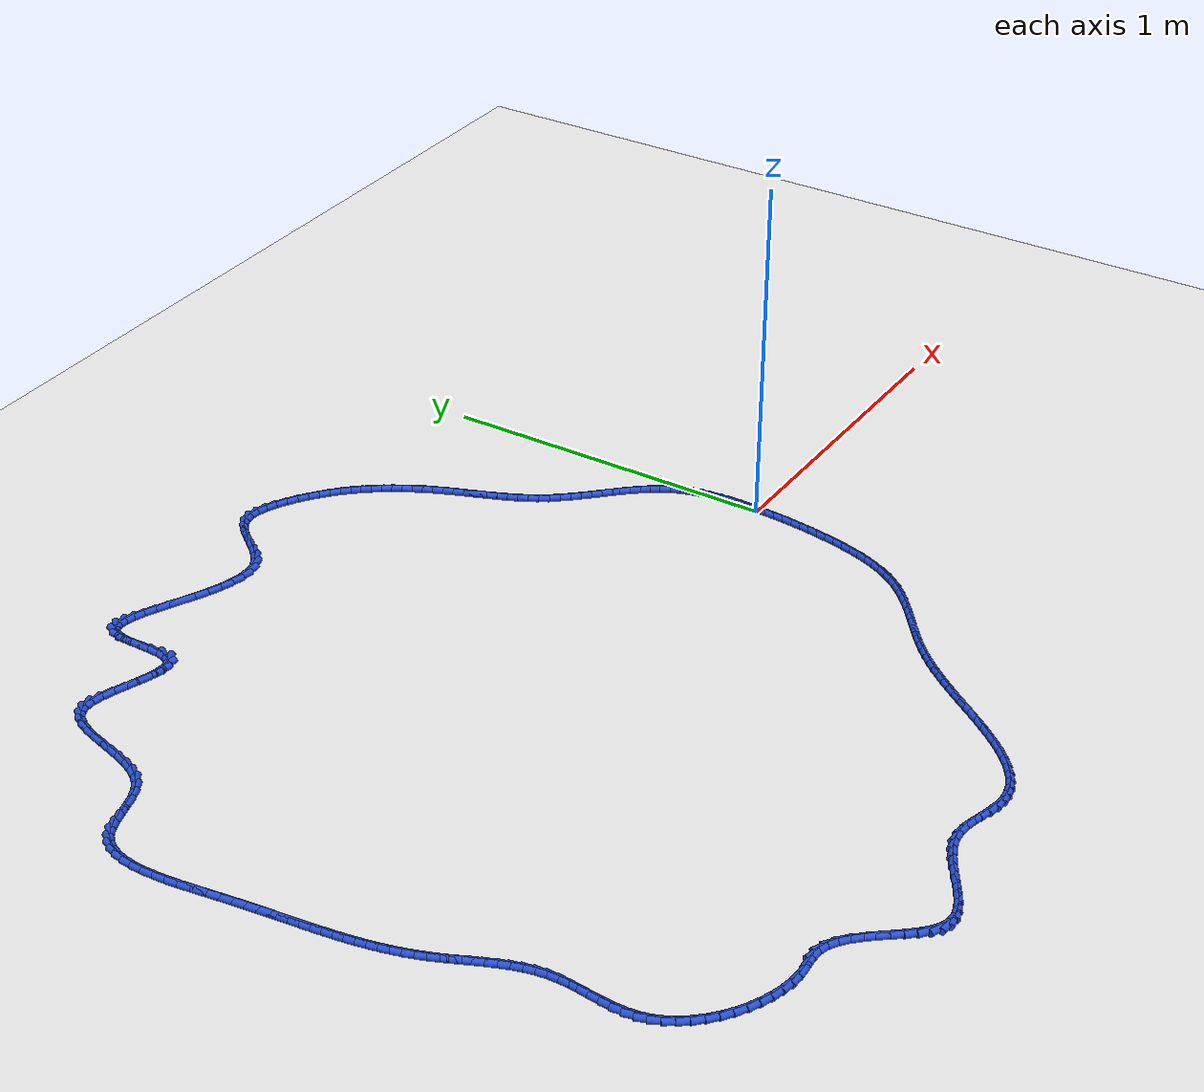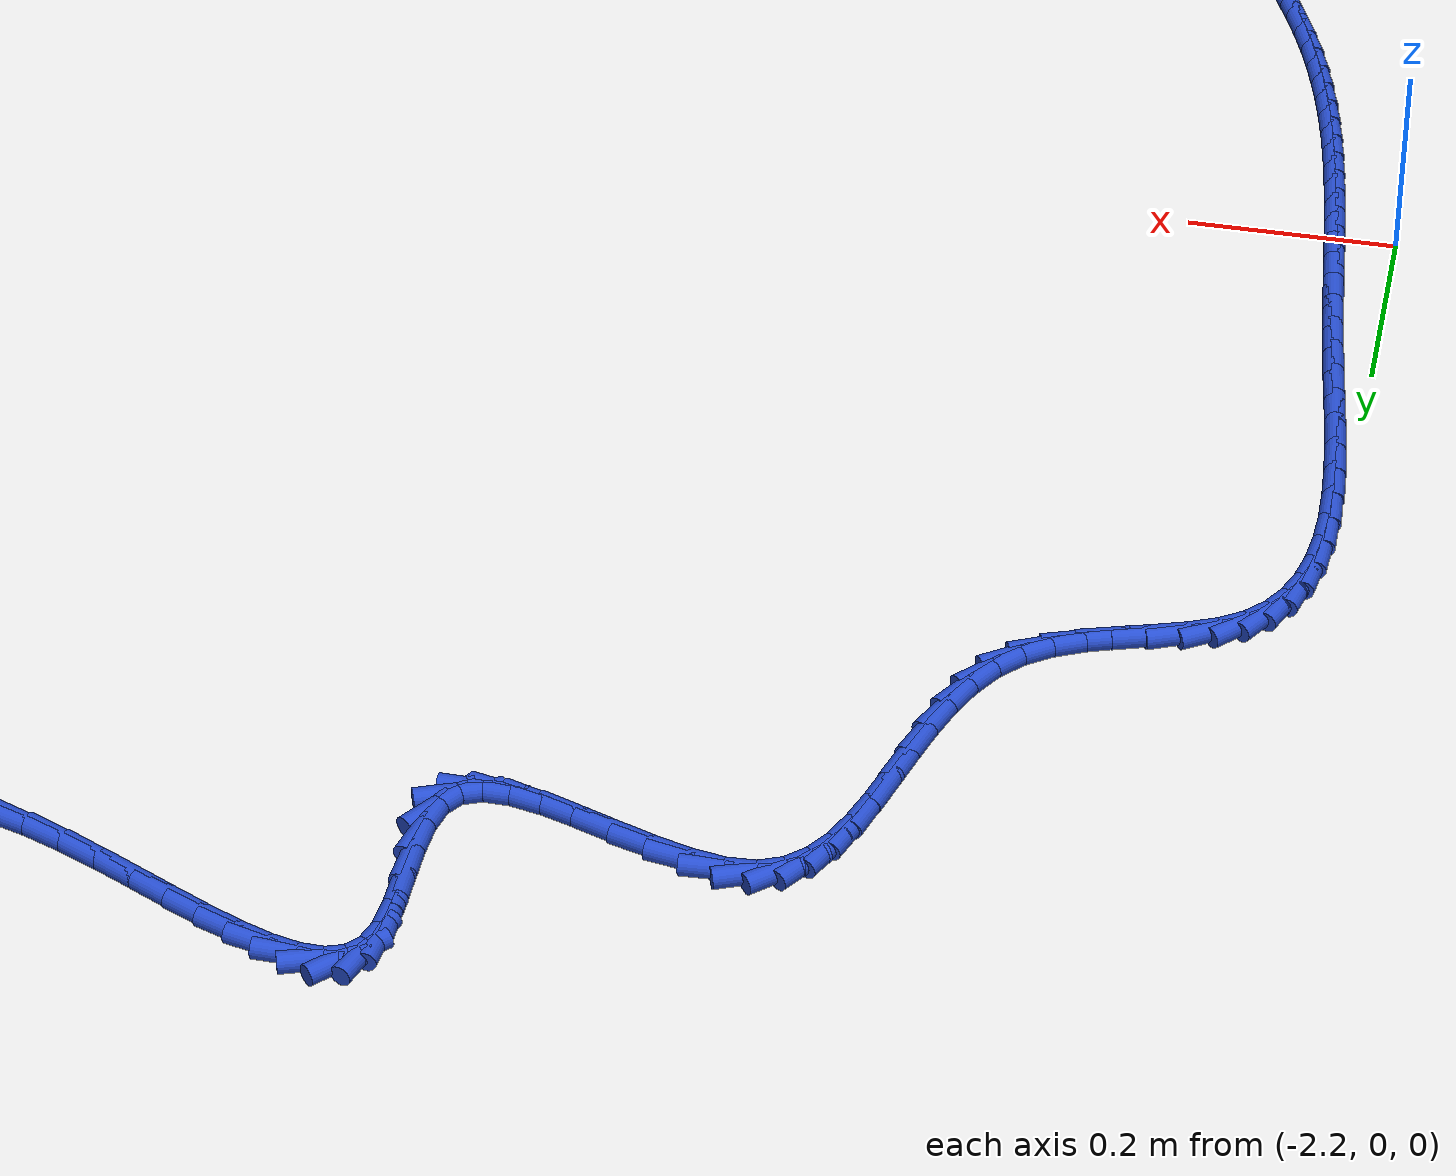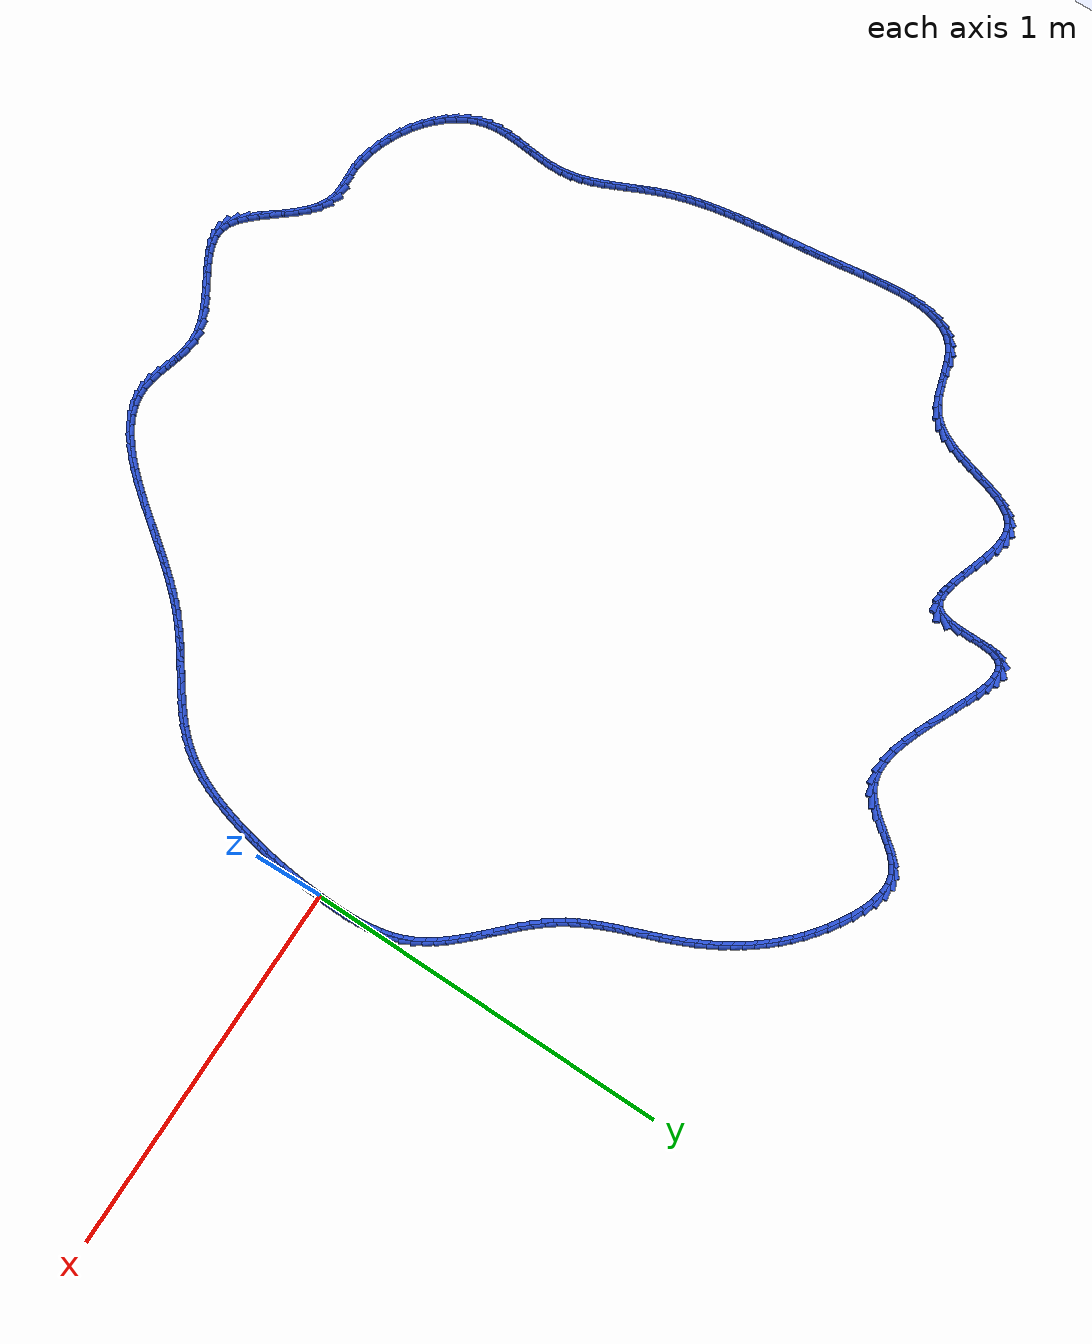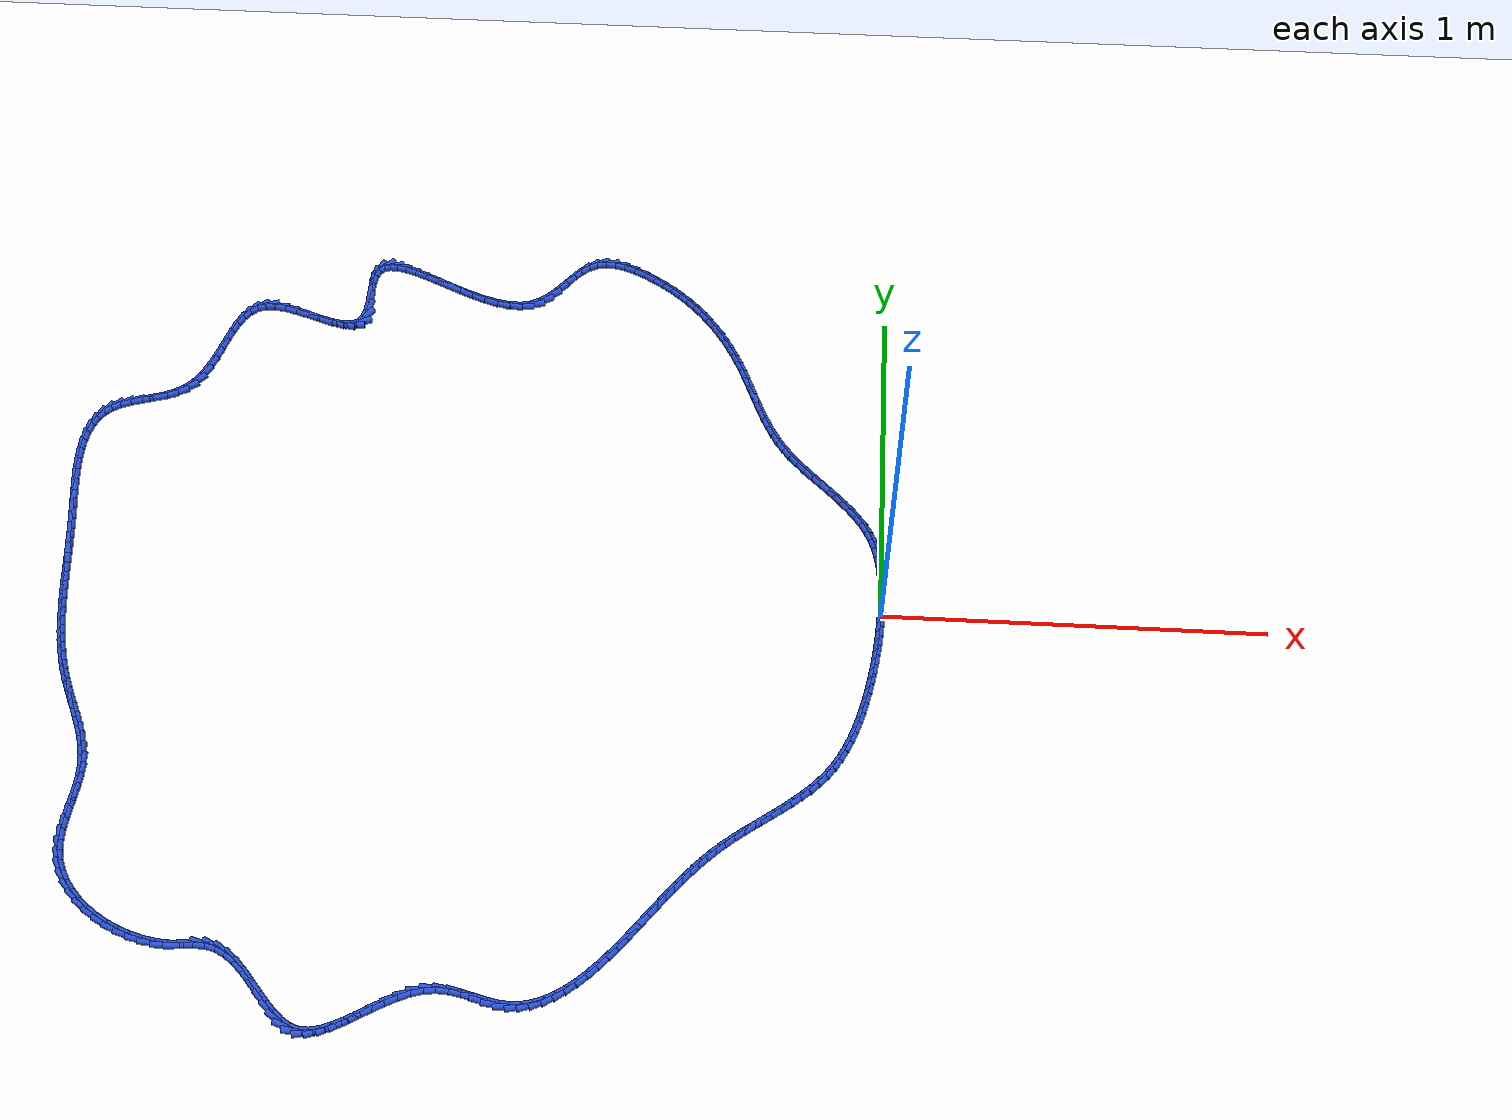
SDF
<sdf version="1.6">
 <world name="default">
  <light name="sun" type="directional">
   <pose>0 0 10 0 -0 0</pose>
   <diffuse>0.8 0.8 0.8 1</diffuse>
   <specular>0.2 0.2 0.2 1</specular>
   <attenuation>
    <range>1000</range>
    <constant>0.9</constant>
    <linear>0.01</linear>
    <quadratic>0.001</quadratic>
   </attenuation>
   <direction>-0.5 0.1 -0.9</direction>
  </light>
  <model name="ground_plane">
   <static>1</static>
   <link name="link">
    <collision name="collision">
     <geometry><plane><normal>0 0 1</normal><size>100 100</size></plane></geometry>
     <surface><friction><ode><mu>100</mu><mu2>50</mu2></ode></friction></surface>
    </collision>
    <visual name="visual">
     <cast_shadows>0</cast_shadows>
     <geometry><plane><normal>0 0 1</normal><size>100 100</size></plane></geometry>
     <material>
      <script><uri>file://media/materials/scripts/gazebo.material</uri><name>Gazebo/WhiteGlow</name></script>
     </material>
    </visual>
   </link>
  </model>
  <gravity>0 0 -9.8</gravity>
  <magnetic_field>6e-06 2.3e-05 -4.2e-05</magnetic_field>
  <atmosphere type="adiabatic"/>
  <physics name="default_physics" default="0" type="ode">
   <max_step_size>0.001</max_step_size>
   <real_time_factor>1</real_time_factor>
   <real_time_update_rate>1000</real_time_update_rate>
  </physics>
  <scene><ambient>0.4 0.4 0.4 1</ambient><background>0.7 0.7 0.7 1</background><shadows>1</shadows></scene>
  <spherical_coordinates>
   <surface_model>EARTH_WGS84</surface_model>
   <latitude_deg>0</latitude_deg>
   <longitude_deg>0</longitude_deg>
   <elevation>0</elevation>
   <heading_deg>0</heading_deg>
  </spherical_coordinates>
  <model name="line">
   <link name="link_0">
    <pose>-2.8731357570865868e-18 -2.7755575615628914e-17 0.01 0 1.57 1.5362780401128615</pose>
    <collision name="collision">
     <geometry><cylinder><radius>0.01</radius><length>0.08</length></cylinder></geometry>
    </collision>
    <visual name="visual">
     <material>
      <script><name>Gazebo/Blue</name><uri>file://media/materials/scripts/gazebo.material</uri></script>
     </material>
     <geometry><cylinder><radius>0.01</radius><length>0.08</length></cylinder></geometry>
    </visual>
   </link>
   <link name="link_1">
    <pose>0.0010563411514584345 0.030590208027844613 0.01 0 1.57 1.5612468713388525</pose>
    <collision name="collision">
     <geometry><cylinder><radius>0.01</radius><length>0.08</length></cylinder></geometry>
    </collision>
    <visual name="visual">
     <material>
      <script><name>Gazebo/Blue</name><uri>file://media/materials/scripts/gazebo.material</uri></script>
     </material>
     <geometry><cylinder><radius>0.01</radius><length>0.08</length></cylinder></geometry>
    </visual>
   </link>
   <link name="link_2">
    <pose>0.0013500231915128062 0.06134307285780924 0.01 0 1.57 -1.5473924140012787</pose>
    <collision name="collision">
     <geometry><cylinder><radius>0.01</radius><length>0.08</length></cylinder></geometry>
    </collision>
    <visual name="visual">
     <material>
      <script><name>Gazebo/Blue</name><uri>file://media/materials/scripts/gazebo.material</uri></script>
     </material>
     <geometry><cylinder><radius>0.01</radius><length>0.08</length></cylinder></geometry>
    </visual>
   </link>
   <link name="link_3">
    <pose>0.0006310597148863172 0.09205726193674625 0.01 0 1.57 -1.5058623569453697</pose>
    <collision name="collision">
     <geometry><cylinder><radius>0.01</radius><length>0.08</length></cylinder></geometry>
    </collision>
    <visual name="visual">
     <material>
      <script><name>Gazebo/Blue</name><uri>file://media/materials/scripts/gazebo.material</uri></script>
     </material>
     <geometry><cylinder><radius>0.01</radius><length>0.08</length></cylinder></geometry>
    </visual>
   </link>
   <link name="link_4">
    <pose>-0.0013505356836978335 0.12253144271150802 0.01 0 1.57 -1.4549706473578157</pose>
    <collision name="collision">
     <geometry><cylinder><radius>0.01</radius><length>0.08</length></cylinder></geometry>
    </collision>
    <visual name="visual">
     <material>
      <script><name>Gazebo/Blue</name><uri>file://media/materials/scripts/gazebo.material</uri></script>
     </material>
     <geometry><cylinder><radius>0.01</radius><length>0.08</length></cylinder></geometry>
    </visual>
   </link>
   <link name="link_5">
    <pose>-0.004844749409516442 0.15256428262894692 0.01 0 1.57 -1.393804755443454</pose>
    <collision name="collision">
     <geometry><cylinder><radius>0.01</radius><length>0.08</length></cylinder></geometry>
    </collision>
    <visual name="visual">
     <material>
      <script><name>Gazebo/Blue</name><uri>file://media/materials/scripts/gazebo.material</uri></script>
     </material>
     <geometry><cylinder><radius>0.01</radius><length>0.08</length></cylinder></geometry>
    </visual>
   </link>
   <link name="link_6">
    <pose>-0.010101567867846304 0.1819544491359154 0.01 0 1.57 -1.32144173350356</pose>
    <collision name="collision">
     <geometry><cylinder><radius>0.01</radius><length>0.08</length></cylinder></geometry>
    </collision>
    <visual name="visual">
     <material>
      <script><name>Gazebo/Blue</name><uri>file://media/materials/scripts/gazebo.material</uri></script>
     </material>
     <geometry><cylinder><radius>0.01</radius><length>0.08</length></cylinder></geometry>
    </visual>
   </link>
   <link name="link_7">
    <pose>-0.01737097746396422 0.2105006096792657 0.01 0 1.57 -1.2371471010910633</pose>
    <collision name="collision">
     <geometry><cylinder><radius>0.01</radius><length>0.08</length></cylinder></geometry>
    </collision>
    <visual name="visual">
     <material>
      <script><name>Gazebo/Blue</name><uri>file://media/materials/scripts/gazebo.material</uri></script>
     </material>
     <geometry><cylinder><radius>0.01</radius><length>0.08</length></cylinder></geometry>
    </visual>
   </link>
   <link name="link_8">
    <pose>-0.02690296460314699 0.23800143170585047 0.01 0 1.57 -1.141547642899739</pose>
    <collision name="collision">
     <geometry><cylinder><radius>0.01</radius><length>0.08</length></cylinder></geometry>
    </collision>
    <visual name="visual">
     <material>
      <script><name>Gazebo/Blue</name><uri>file://media/materials/scripts/gazebo.material</uri></script>
     </material>
     <geometry><cylinder><radius>0.01</radius><length>0.08</length></cylinder></geometry>
    </visual>
   </link>
   <link name="link_9">
    <pose>-0.038926152110613454 0.2642694510574671 0.01 0 1.57 -1.0485164768581037</pose>
    <collision name="collision">
     <geometry><cylinder><radius>0.01</radius><length>0.08</length></cylinder></geometry>
    </collision>
    <visual name="visual">
     <material>
      <script><name>Gazebo/Blue</name><uri>file://media/materials/scripts/gazebo.material</uri></script>
     </material>
     <geometry><cylinder><radius>0.01</radius><length>0.08</length></cylinder></geometry>
    </visual>
   </link>
   <link name="link_10">
    <pose>-0.05334825386540836 0.2893255250274168 0.01 0 1.57 -0.9695458577225404</pose>
    <collision name="collision">
     <geometry><cylinder><radius>0.01</radius><length>0.08</length></cylinder></geometry>
    </collision>
    <visual name="visual">
     <material>
      <script><name>Gazebo/Blue</name><uri>file://media/materials/scripts/gazebo.material</uri></script>
     </material>
     <geometry><cylinder><radius>0.01</radius><length>0.08</length></cylinder></geometry>
    </visual>
   </link>
   <link name="link_11">
    <pose>-0.06982930833393573 0.31335129203423384 0.01 0 1.57 -0.9053663184407817</pose>
    <collision name="collision">
     <geometry><cylinder><radius>0.01</radius><length>0.08</length></cylinder></geometry>
    </collision>
    <visual name="visual">
     <material>
      <script><name>Gazebo/Blue</name><uri>file://media/materials/scripts/gazebo.material</uri></script>
     </material>
     <geometry><cylinder><radius>0.01</radius><length>0.08</length></cylinder></geometry>
    </visual>
   </link>
   <link name="link_12">
    <pose>-0.08802294588776693 0.33653255037928725 0.01 0 1.57 -0.8556844754677903</pose>
    <collision name="collision">
     <geometry><cylinder><radius>0.01</radius><length>0.08</length></cylinder></geometry>
    </collision>
    <visual name="visual">
     <material>
      <script><name>Gazebo/Blue</name><uri>file://media/materials/scripts/gazebo.material</uri></script>
     </material>
     <geometry><cylinder><radius>0.01</radius><length>0.08</length></cylinder></geometry>
    </visual>
   </link>
   <link name="link_13">
    <pose>-0.10758279689847325 0.3590550983639467 0.01 0 1.57 -0.8198664247431035</pose>
    <collision name="collision">
     <geometry><cylinder><radius>0.01</radius><length>0.08</length></cylinder></geometry>
    </collision>
    <visual name="visual">
     <material>
      <script><name>Gazebo/Blue</name><uri>file://media/materials/scripts/gazebo.material</uri></script>
     </material>
     <geometry><cylinder><radius>0.01</radius><length>0.08</length></cylinder></geometry>
    </visual>
   </link>
   <link name="link_14">
    <pose>-0.12816249173762606 0.38110473428958136 0.01 0 1.57 -0.7972387106667777</pose>
    <collision name="collision">
     <geometry><cylinder><radius>0.01</radius><length>0.08</length></cylinder></geometry>
    </collision>
    <visual name="visual">
     <material>
      <script><name>Gazebo/Blue</name><uri>file://media/materials/scripts/gazebo.material</uri></script>
     </material>
     <geometry><cylinder><radius>0.01</radius><length>0.08</length></cylinder></geometry>
    </visual>
   </link>
   <link name="link_15">
    <pose>-0.14941566077679663 0.40286725645756055 0.01 0 1.57 -0.7872698154737598</pose>
    <collision name="collision">
     <geometry><cylinder><radius>0.01</radius><length>0.08</length></cylinder></geometry>
    </collision>
    <visual name="visual">
     <material>
      <script><name>Gazebo/Blue</name><uri>file://media/materials/scripts/gazebo.material</uri></script>
     </material>
     <geometry><cylinder><radius>0.01</radius><length>0.08</length></cylinder></geometry>
    </visual>
   </link>
   <link name="link_16">
    <pose>-0.17099593438755648 0.4245284631692538 0.01 0 1.57 -0.7896626280506444</pose>
    <collision name="collision">
     <geometry><cylinder><radius>0.01</radius><length>0.08</length></cylinder></geometry>
    </collision>
    <visual name="visual">
     <material>
      <script><name>Gazebo/Blue</name><uri>file://media/materials/scripts/gazebo.material</uri></script>
     </material>
     <geometry><cylinder><radius>0.01</radius><length>0.08</length></cylinder></geometry>
    </visual>
   </link>
   <link name="link_17">
    <pose>-0.19255694294147682 0.44627415272603044 0.01 0 1.57 -0.8043861911847339</pose>
    <collision name="collision">
     <geometry><cylinder><radius>0.01</radius><length>0.08</length></cylinder></geometry>
    </collision>
    <visual name="visual">
     <material>
      <script><name>Gazebo/Blue</name><uri>file://media/materials/scripts/gazebo.material</uri></script>
     </material>
     <geometry><cylinder><radius>0.01</radius><length>0.08</length></cylinder></geometry>
    </visual>
   </link>
   <link name="link_18">
    <pose>-0.21375231681012902 0.4682901234292598 0.01 0 1.57 -0.8316615131173729</pose>
    <collision name="collision">
     <geometry><cylinder><radius>0.01</radius><length>0.08</length></cylinder></geometry>
    </collision>
    <visual name="visual">
     <material>
      <script><name>Gazebo/Blue</name><uri>file://media/materials/scripts/gazebo.material</uri></script>
     </material>
     <geometry><cylinder><radius>0.01</radius><length>0.08</length></cylinder></geometry>
    </visual>
   </link>
   <link name="link_19">
    <pose>-0.23423568636508435 0.4907621735803111 0.01 0 1.57 -0.8719007435504268</pose>
    <collision name="collision">
     <geometry><cylinder><radius>0.01</radius><length>0.08</length></cylinder></geometry>
    </collision>
    <visual name="visual">
     <material>
      <script><name>Gazebo/Blue</name><uri>file://media/materials/scripts/gazebo.material</uri></script>
     </material>
     <geometry><cylinder><radius>0.01</radius><length>0.08</length></cylinder></geometry>
    </visual>
   </link>
   <link name="link_20">
    <pose>-0.2536606819779143 0.513876101480554 0.01 0 1.57 -0.9255852740462283</pose>
    <collision name="collision">
     <geometry><cylinder><radius>0.01</radius><length>0.08</length></cylinder></geometry>
    </collision>
    <visual name="visual">
     <material>
      <script><name>Gazebo/Blue</name><uri>file://media/materials/scripts/gazebo.material</uri></script>
     </material>
     <geometry><cylinder><radius>0.01</radius><length>0.08</length></cylinder></geometry>
    </visual>
   </link>
   <link name="link_21">
    <pose>-0.27168093402019006 0.5378177054313575 0.01 0 1.57 -0.989496703409248</pose>
    <collision name="collision">
     <geometry><cylinder><radius>0.01</radius><length>0.08</length></cylinder></geometry>
    </collision>
    <visual name="visual">
     <material>
      <script><name>Gazebo/Blue</name><uri>file://media/materials/scripts/gazebo.material</uri></script>
     </material>
     <geometry><cylinder><radius>0.01</radius><length>0.08</length></cylinder></geometry>
    </visual>
   </link>
   <link name="link_22">
    <pose>-0.28804299897083524 0.5627208709837269 0.01 0 1.57 -1.0482772937960567</pose>
    <collision name="collision">
     <geometry><cylinder><radius>0.01</radius><length>0.08</length></cylinder></geometry>
    </collision>
    <visual name="visual">
     <material>
      <script><name>Gazebo/Blue</name><uri>file://media/materials/scripts/gazebo.material</uri></script>
     </material>
     <geometry><cylinder><radius>0.01</radius><length>0.08</length></cylinder></geometry>
    </visual>
   </link>
   <link name="link_23">
    <pose>-0.3028887226538286 0.5884986570805574 0.01 0 1.57 -1.0974497386944173</pose>
    <collision name="collision">
     <geometry><cylinder><radius>0.01</radius><length>0.08</length></cylinder></geometry>
    </collision>
    <visual name="visual">
     <material>
      <script><name>Gazebo/Blue</name><uri>file://media/materials/scripts/gazebo.material</uri></script>
     </material>
     <geometry><cylinder><radius>0.01</radius><length>0.08</length></cylinder></geometry>
    </visual>
   </link>
   <link name="link_24">
    <pose>-0.3164650388248105 0.6150054157661312 0.01 0 1.57 -1.136845922140829</pose>
    <collision name="collision">
     <geometry><cylinder><radius>0.01</radius><length>0.08</length></cylinder></geometry>
    </collision>
    <visual name="visual">
     <material>
      <script><name>Gazebo/Blue</name><uri>file://media/materials/scripts/gazebo.material</uri></script>
     </material>
     <geometry><cylinder><radius>0.01</radius><length>0.08</length></cylinder></geometry>
    </visual>
   </link>
   <link name="link_25">
    <pose>-0.32901888209148666 0.64209549860873 0.01 0 1.57 -1.1664971877787347</pose>
    <collision name="collision">
     <geometry><cylinder><radius>0.01</radius><length>0.08</length></cylinder></geometry>
    </collision>
    <visual name="visual">
     <material>
      <script><name>Gazebo/Blue</name><uri>file://media/materials/scripts/gazebo.material</uri></script>
     </material>
     <geometry><cylinder><radius>0.01</radius><length>0.08</length></cylinder></geometry>
    </visual>
   </link>
   <link name="link_26">
    <pose>-0.34079718706156253 0.6696232571766353 0.01 0 1.57 -1.1865217684535214</pose>
    <collision name="collision">
     <geometry><cylinder><radius>0.01</radius><length>0.08</length></cylinder></geometry>
    </collision>
    <visual name="visual">
     <material>
      <script><name>Gazebo/Blue</name><uri>file://media/materials/scripts/gazebo.material</uri></script>
     </material>
     <geometry><cylinder><radius>0.01</radius><length>0.08</length></cylinder></geometry>
    </visual>
   </link>
   <link name="link_27">
    <pose>-0.3520468883427435 0.6974430430381275 0.01 0 1.57 -1.1970413427886664</pose>
    <collision name="collision">
     <geometry><cylinder><radius>0.01</radius><length>0.08</length></cylinder></geometry>
    </collision>
    <visual name="visual">
     <material>
      <script><name>Gazebo/Blue</name><uri>file://media/materials/scripts/gazebo.material</uri></script>
     </material>
     <geometry><cylinder><radius>0.01</radius><length>0.08</length></cylinder></geometry>
    </visual>
   </link>
   <link name="link_28">
    <pose>-0.3630149205427351 0.7254092077614883 0.01 0 1.57 -1.1981271007819305</pose>
    <collision name="collision">
     <geometry><cylinder><radius>0.01</radius><length>0.08</length></cylinder></geometry>
    </collision>
    <visual name="visual">
     <material>
      <script><name>Gazebo/Blue</name><uri>file://media/materials/scripts/gazebo.material</uri></script>
     </material>
     <geometry><cylinder><radius>0.01</radius><length>0.08</length></cylinder></geometry>
    </visual>
   </link>
   <link name="link_29">
    <pose>-0.37394821826924296 0.753376102914999 0.01 0 1.57 -1.1897723875010986</pose>
    <collision name="collision">
     <geometry><cylinder><radius>0.01</radius><length>0.08</length></cylinder></geometry>
    </collision>
    <visual name="visual">
     <material>
      <script><name>Gazebo/Blue</name><uri>file://media/materials/scripts/gazebo.material</uri></script>
     </material>
     <geometry><cylinder><radius>0.01</radius><length>0.08</length></cylinder></geometry>
    </visual>
   </link>
   <link name="link_30">
    <pose>-0.38509371612997206 0.78119808006694 0.01 0 1.57 -1.1718906123453805</pose>
    <collision name="collision">
     <geometry><cylinder><radius>0.01</radius><length>0.08</length></cylinder></geometry>
    </collision>
    <visual name="visual">
     <material>
      <script><name>Gazebo/Blue</name><uri>file://media/materials/scripts/gazebo.material</uri></script>
     </material>
     <geometry><cylinder><radius>0.01</radius><length>0.08</length></cylinder></geometry>
    </visual>
   </link>
   <link name="link_31">
    <pose>-0.39669832065502636 0.8087295072804076 0.01 0 1.57 -1.1458802670632349</pose>
    <collision name="collision">
     <geometry><cylinder><radius>0.01</radius><length>0.08</length></cylinder></geometry>
    </collision>
    <visual name="visual">
     <material>
      <script><name>Gazebo/Blue</name><uri>file://media/materials/scripts/gazebo.material</uri></script>
     </material>
     <geometry><cylinder><radius>0.01</radius><length>0.08</length></cylinder></geometry>
    </visual>
   </link>
   <link name="link_32">
    <pose>-0.4089690383214071 0.8358481927954906 0.01 0 1.57 -1.1162702524143353</pose>
    <collision name="collision">
     <geometry><cylinder><radius>0.01</radius><length>0.08</length></cylinder></geometry>
    </collision>
    <visual name="visual">
     <material>
      <script><name>Gazebo/Blue</name><uri>file://media/materials/scripts/gazebo.material</uri></script>
     </material>
     <geometry><cylinder><radius>0.01</radius><length>0.08</length></cylinder></geometry>
    </visual>
   </link>
   <link name="link_33">
    <pose>-0.4219934574967669 0.8625020996867165 0.01 0 1.57 -1.0839191640420225</pose>
    <collision name="collision">
     <geometry><cylinder><radius>0.01</radius><length>0.08</length></cylinder></geometry>
    </collision>
    <visual name="visual">
     <material>
      <script><name>Gazebo/Blue</name><uri>file://media/materials/scripts/gazebo.material</uri></script>
     </material>
     <geometry><cylinder><radius>0.01</radius><length>0.08</length></cylinder></geometry>
    </visual>
   </link>
   <link name="link_34">
    <pose>-0.4358369209933022 0.8886522596768136 0.01 0 1.57 -1.0488572850521165</pose>
    <collision name="collision">
     <geometry><cylinder><radius>0.01</radius><length>0.08</length></cylinder></geometry>
    </collision>
    <visual name="visual">
     <material>
      <script><name>Gazebo/Blue</name><uri>file://media/materials/scripts/gazebo.material</uri></script>
     </material>
     <geometry><cylinder><radius>0.01</radius><length>0.08</length></cylinder></geometry>
    </visual>
   </link>
   <link name="link_35">
    <pose>-0.4505647716232093 0.9142597044885112 0.01 0 1.57 -1.0111494737315954</pose>
    <collision name="collision">
     <geometry><cylinder><radius>0.01</radius><length>0.08</length></cylinder></geometry>
    </collision>
    <visual name="visual">
     <material>
      <script><name>Gazebo/Blue</name><uri>file://media/materials/scripts/gazebo.material</uri></script>
     </material>
     <geometry><cylinder><radius>0.01</radius><length>0.08</length></cylinder></geometry>
    </visual>
   </link>
   <link name="link_36">
    <pose>-0.4662423521986848 0.9392854658445384 0.01 0 1.57 -0.9709018523709882</pose>
    <collision name="collision">
     <geometry><cylinder><radius>0.01</radius><length>0.08</length></cylinder></geometry>
    </collision>
    <visual name="visual">
     <material>
      <script><name>Gazebo/Blue</name><uri>file://media/materials/scripts/gazebo.material</uri></script>
     </material>
     <geometry><cylinder><radius>0.01</radius><length>0.08</length></cylinder></geometry>
    </visual>
   </link>
   <link name="link_37">
    <pose>-0.48293500553192503 0.9636905754676239 0.01 0 1.57 -0.9282675177149626</pose>
    <collision name="collision">
     <geometry><cylinder><radius>0.01</radius><length>0.08</length></cylinder></geometry>
    </collision>
    <visual name="visual">
     <material>
      <script><name>Gazebo/Blue</name><uri>file://media/materials/scripts/gazebo.material</uri></script>
     </material>
     <geometry><cylinder><radius>0.01</radius><length>0.08</length></cylinder></geometry>
    </visual>
   </link>
   <link name="link_38">
    <pose>-0.5007080744351264 0.9874360650804972 0.01 0 1.57 -0.8834504608222832</pose>
    <collision name="collision">
     <geometry><cylinder><radius>0.01</radius><length>0.08</length></cylinder></geometry>
    </collision>
    <visual name="visual">
     <material>
      <script><name>Gazebo/Blue</name><uri>file://media/materials/scripts/gazebo.material</uri></script>
     </material>
     <geometry><cylinder><radius>0.01</radius><length>0.08</length></cylinder></geometry>
    </visual>
   </link>
   <link name="link_39">
    <pose>-0.5196269017204855 1.0104829664058868 0.01 0 1.57 -0.8367068518344898</pose>
    <collision name="collision">
     <geometry><cylinder><radius>0.01</radius><length>0.08</length></cylinder></geometry>
    </collision>
    <visual name="visual">
     <material>
      <script><name>Gazebo/Blue</name><uri>file://media/materials/scripts/gazebo.material</uri></script>
     </material>
     <geometry><cylinder><radius>0.01</radius><length>0.08</length></cylinder></geometry>
    </visual>
   </link>
   <link name="link_40">
    <pose>-0.5397568302001985 1.0327923111665216 0.01 0 1.57 -0.788342957180331</pose>
    <collision name="collision">
     <geometry><cylinder><radius>0.01</radius><length>0.08</length></cylinder></geometry>
    </collision>
    <visual name="visual">
     <material>
      <script><name>Gazebo/Blue</name><uri>file://media/materials/scripts/gazebo.material</uri></script>
     </material>
     <geometry><cylinder><radius>0.01</radius><length>0.08</length></cylinder></geometry>
    </visual>
   </link>
   <link name="link_41">
    <pose>-0.5611632026864619 1.0543251310851305 0.01 0 1.57 -0.7387092423080179</pose>
    <collision name="collision">
     <geometry><cylinder><radius>0.01</radius><length>0.08</length></cylinder></geometry>
    </collision>
    <visual name="visual">
     <material>
      <script><name>Gazebo/Blue</name><uri>file://media/materials/scripts/gazebo.material</uri></script>
     </material>
     <geometry><cylinder><radius>0.01</radius><length>0.08</length></cylinder></geometry>
    </visual>
   </link>
   <link name="link_42">
    <pose>-0.5839113619914722 1.075042457884443 0.01 0 1.57 -0.6881906602183026</pose>
    <collision name="collision">
     <geometry><cylinder><radius>0.01</radius><length>0.08</length></cylinder></geometry>
    </collision>
    <visual name="visual">
     <material>
      <script><name>Gazebo/Blue</name><uri>file://media/materials/scripts/gazebo.material</uri></script>
     </material>
     <geometry><cylinder><radius>0.01</radius><length>0.08</length></cylinder></geometry>
    </visual>
   </link>
   <link name="link_43">
    <pose>-0.6080666509274257 1.094905323287188 0.01 0 1.57 -0.6371936695155282</pose>
    <collision name="collision">
     <geometry><cylinder><radius>0.01</radius><length>0.08</length></cylinder></geometry>
    </collision>
    <visual name="visual">
     <material>
      <script><name>Gazebo/Blue</name><uri>file://media/materials/scripts/gazebo.material</uri></script>
     </material>
     <geometry><cylinder><radius>0.01</radius><length>0.08</length></cylinder></geometry>
    </visual>
   </link>
   <link name="link_44">
    <pose>-0.6336944123065187 1.1138747590160936 0.01 0 1.57 -0.586131053227736</pose>
    <collision name="collision">
     <geometry><cylinder><radius>0.01</radius><length>0.08</length></cylinder></geometry>
    </collision>
    <visual name="visual">
     <material>
      <script><name>Gazebo/Blue</name><uri>file://media/materials/scripts/gazebo.material</uri></script>
     </material>
     <geometry><cylinder><radius>0.01</radius><length>0.08</length></cylinder></geometry>
    </visual>
   </link>
   <link name="link_45">
    <pose>-0.6608599889409479 1.1319117967938894 0.01 0 1.57 -0.5342552924577152</pose>
    <collision name="collision">
     <geometry><cylinder><radius>0.01</radius><length>0.08</length></cylinder></geometry>
    </collision>
    <visual name="visual">
     <material>
      <script><name>Gazebo/Blue</name><uri>file://media/materials/scripts/gazebo.material</uri></script>
     </material>
     <geometry><cylinder><radius>0.01</radius><length>0.08</length></cylinder></geometry>
    </visual>
   </link>
   <link name="link_46">
    <pose>-0.6895772070718386 1.1489022660639547 0.01 0 1.57 -0.46902416908908207</pose>
    <collision name="collision">
     <geometry><cylinder><radius>0.01</radius><length>0.08</length></cylinder></geometry>
    </collision>
    <visual name="visual">
     <material>
      <script><name>Gazebo/Blue</name><uri>file://media/materials/scripts/gazebo.material</uri></script>
     </material>
     <geometry><cylinder><radius>0.01</radius><length>0.08</length></cylinder></geometry>
    </visual>
   </link>
   <link name="link_47">
    <pose>-0.7193517075398492 1.1639901631147707 0.01 0 1.57 -0.3772798454977268</pose>
    <collision name="collision">
     <geometry><cylinder><radius>0.01</radius><length>0.08</length></cylinder></geometry>
    </collision>
    <visual name="visual">
     <material>
      <script><name>Gazebo/Blue</name><uri>file://media/materials/scripts/gazebo.material</uri></script>
     </material>
     <geometry><cylinder><radius>0.01</radius><length>0.08</length></cylinder></geometry>
    </visual>
   </link>
   <link name="link_48">
    <pose>-0.7493997565128359 1.1758970641371986 0.01 0 1.57 -0.24685653449712952</pose>
    <collision name="collision">
     <geometry><cylinder><radius>0.01</radius><length>0.08</length></cylinder></geometry>
    </collision>
    <visual name="visual">
     <material>
      <script><name>Gazebo/Blue</name><uri>file://media/materials/scripts/gazebo.material</uri></script>
     </material>
     <geometry><cylinder><radius>0.01</radius><length>0.08</length></cylinder></geometry>
    </visual>
   </link>
   <link name="link_49">
    <pose>-0.7789342648536896 1.1833396473528466 0.01 0 1.57 -0.05996030256032076</pose>
    <collision name="collision">
     <geometry><cylinder><radius>0.01</radius><length>0.08</length></cylinder></geometry>
    </collision>
    <visual name="visual">
     <material>
      <script><name>Gazebo/Blue</name><uri>file://media/materials/scripts/gazebo.material</uri></script>
     </material>
     <geometry><cylinder><radius>0.01</radius><length>0.08</length></cylinder></geometry>
    </visual>
   </link>
   <link name="link_50">
    <pose>-0.8071681434253017 1.1850345909833218 0.01 0 1.57 0.20130925087797083</pose>
    <collision name="collision">
     <geometry><cylinder><radius>0.01</radius><length>0.08</length></cylinder></geometry>
    </collision>
    <visual name="visual">
     <material>
      <script><name>Gazebo/Blue</name><uri>file://media/materials/scripts/gazebo.material</uri></script>
     </material>
     <geometry><cylinder><radius>0.01</radius><length>0.08</length></cylinder></geometry>
    </visual>
   </link>
   <link name="link_51">
    <pose>-0.8333144244419122 1.1796988292662336 0.01 0 1.57 0.5023566198429702</pose>
    <collision name="collision">
     <geometry><cylinder><radius>0.01</radius><length>0.08</length></cylinder></geometry>
    </collision>
    <visual name="visual">
     <material>
      <script><name>Gazebo/Blue</name><uri>file://media/materials/scripts/gazebo.material</uri></script>
     </material>
     <geometry><cylinder><radius>0.01</radius><length>0.08</length></cylinder></geometry>
    </visual>
   </link>
   <link name="link_52">
    <pose>-0.8569113789614968 1.166735455673453 0.01 0 1.57 0.7212849251761181</pose>
    <collision name="collision">
     <geometry><cylinder><radius>0.01</radius><length>0.08</length></cylinder></geometry>
    </collision>
    <visual name="visual">
     <material>
      <script><name>Gazebo/Blue</name><uri>file://media/materials/scripts/gazebo.material</uri></script>
     </material>
     <geometry><cylinder><radius>0.01</radius><length>0.08</length></cylinder></geometry>
    </visual>
   </link>
   <link name="link_53">
    <pose>-0.8785296482813488 1.1477255642033257 0.01 0 1.57 0.8458318410964321</pose>
    <collision name="collision">
     <geometry><cylinder><radius>0.01</radius><length>0.08</length></cylinder></geometry>
    </collision>
    <visual name="visual">
     <material>
      <script><name>Gazebo/Blue</name><uri>file://media/materials/scripts/gazebo.material</uri></script>
     </material>
     <geometry><cylinder><radius>0.01</radius><length>0.08</length></cylinder></geometry>
    </visual>
   </link>
   <link name="link_54">
    <pose>-0.8989442386502885 1.1246813993804947 0.01 0 1.57 0.8976882505367142</pose>
    <collision name="collision">
     <geometry><cylinder><radius>0.01</radius><length>0.08</length></cylinder></geometry>
    </collision>
    <visual name="visual">
     <material>
      <script><name>Gazebo/Blue</name><uri>file://media/materials/scripts/gazebo.material</uri></script>
     </material>
     <geometry><cylinder><radius>0.01</radius><length>0.08</length></cylinder></geometry>
    </visual>
   </link>
   <link name="link_55">
    <pose>-0.9189301563171345 1.0996152057296007 0.01 0 1.57 0.8894890259017091</pose>
    <collision name="collision">
     <geometry><cylinder><radius>0.01</radius><length>0.08</length></cylinder></geometry>
    </collision>
    <visual name="visual">
     <material>
      <script><name>Gazebo/Blue</name><uri>file://media/materials/scripts/gazebo.material</uri></script>
     </material>
     <geometry><cylinder><radius>0.01</radius><length>0.08</length></cylinder></geometry>
    </visual>
   </link>
   <link name="link_56">
    <pose>-0.9392624075307069 1.074539227775287 0.01 0 1.57 0.8217628106823327</pose>
    <collision name="collision">
     <geometry><cylinder><radius>0.01</radius><length>0.08</length></cylinder></geometry>
    </collision>
    <visual name="visual">
     <material>
      <script><name>Gazebo/Blue</name><uri>file://media/materials/scripts/gazebo.material</uri></script>
     </material>
     <geometry><cylinder><radius>0.01</radius><length>0.08</length></cylinder></geometry>
    </visual>
   </link>
   <link name="link_57">
    <pose>-0.9607159985398246 1.0514657100421954 0.01 0 1.57 0.6845565056192284</pose>
    <collision name="collision">
     <geometry><cylinder><radius>0.01</radius><length>0.08</length></cylinder></geometry>
    </collision>
    <visual name="visual">
     <material>
      <script><name>Gazebo/Blue</name><uri>file://media/materials/scripts/gazebo.material</uri></script>
     </material>
     <geometry><cylinder><radius>0.01</radius><length>0.08</length></cylinder></geometry>
    </visual>
   </link>
   <link name="link_58">
    <pose>-0.9840659355933067 1.0324068970549678 0.01 0 1.57 0.464382555857606</pose>
    <collision name="collision">
     <geometry><cylinder><radius>0.01</radius><length>0.08</length></cylinder></geometry>
    </collision>
    <visual name="visual">
     <material>
      <script><name>Gazebo/Blue</name><uri>file://media/materials/scripts/gazebo.material</uri></script>
     </material>
     <geometry><cylinder><radius>0.01</radius><length>0.08</length></cylinder></geometry>
    </visual>
   </link>
   <link name="link_59">
    <pose>-1.0100862551189302 1.0193728240603128 0.01 0 1.57 0.1966385221647778</pose>
    <collision name="collision">
     <geometry><cylinder><radius>0.01</radius><length>0.08</length></cylinder></geometry>
    </collision>
    <visual name="visual">
     <material>
      <script><name>Gazebo/Blue</name><uri>file://media/materials/scripts/gazebo.material</uri></script>
     </material>
     <geometry><cylinder><radius>0.01</radius><length>0.08</length></cylinder></geometry>
    </visual>
   </link>
   <link name="link_60">
    <pose>-1.03919961234353 1.0135730706547084 0.01 0 1.57 -0.020727958827722853</pose>
    <collision name="collision">
     <geometry><cylinder><radius>0.01</radius><length>0.08</length></cylinder></geometry>
    </collision>
    <visual name="visual">
     <material>
      <script><name>Gazebo/Blue</name><uri>file://media/materials/scripts/gazebo.material</uri></script>
     </material>
     <geometry><cylinder><radius>0.01</radius><length>0.08</length></cylinder></geometry>
    </visual>
   </link>
   <link name="link_61">
    <pose>-1.0709569488337016 1.0142314297082666 0.01 0 1.57 -0.1766634335091765</pose>
    <collision name="collision">
     <geometry><cylinder><radius>0.01</radius><length>0.08</length></cylinder></geometry>
    </collision>
    <visual name="visual">
     <material>
      <script><name>Gazebo/Blue</name><uri>file://media/materials/scripts/gazebo.material</uri></script>
     </material>
     <geometry><cylinder><radius>0.01</radius><length>0.08</length></cylinder></geometry>
    </visual>
   </link>
   <link name="link_62">
    <pose>-1.1047763400410704 1.0202690215742825 0.01 0 1.57 -0.2848968509468549</pose>
    <collision name="collision">
     <geometry><cylinder><radius>0.01</radius><length>0.08</length></cylinder></geometry>
    </collision>
    <visual name="visual">
     <material>
      <script><name>Gazebo/Blue</name><uri>file://media/materials/scripts/gazebo.material</uri></script>
     </material>
     <geometry><cylinder><radius>0.01</radius><length>0.08</length></cylinder></geometry>
    </visual>
   </link>
   <link name="link_63">
    <pose>-1.140075861417262 1.0306069666060504 0.01 0 1.57 -0.3584138830336988</pose>
    <collision name="collision">
     <geometry><cylinder><radius>0.01</radius><length>0.08</length></cylinder></geometry>
    </collision>
    <visual name="visual">
     <material>
      <script><name>Gazebo/Blue</name><uri>file://media/materials/scripts/gazebo.material</uri></script>
     </material>
     <geometry><cylinder><radius>0.01</radius><length>0.08</length></cylinder></geometry>
    </visual>
   </link>
   <link name="link_64">
    <pose>-1.1762735884139017 1.0441663851568648 0.01 0 1.57 -0.4061209159079297</pose>
    <collision name="collision">
     <geometry><cylinder><radius>0.01</radius><length>0.08</length></cylinder></geometry>
    </collision>
    <visual name="visual">
     <material>
      <script><name>Gazebo/Blue</name><uri>file://media/materials/scripts/gazebo.material</uri></script>
     </material>
     <geometry><cylinder><radius>0.01</radius><length>0.08</length></cylinder></geometry>
    </visual>
   </link>
   <link name="link_65">
    <pose>-1.2127875964826167 1.0598683975800214 0.01 0 1.57 -0.43321966788153526</pose>
    <collision name="collision">
     <geometry><cylinder><radius>0.01</radius><length>0.08</length></cylinder></geometry>
    </collision>
    <visual name="visual">
     <material>
      <script><name>Gazebo/Blue</name><uri>file://media/materials/scripts/gazebo.material</uri></script>
     </material>
     <geometry><cylinder><radius>0.01</radius><length>0.08</length></cylinder></geometry>
    </visual>
   </link>
   <link name="link_66">
    <pose>-1.2490359610750312 1.0766341242288142 0.01 0 1.57 -0.44195338461217365</pose>
    <collision name="collision">
     <geometry><cylinder><radius>0.01</radius><length>0.08</length></cylinder></geometry>
    </collision>
    <visual name="visual">
     <material>
      <script><name>Gazebo/Blue</name><uri>file://media/materials/scripts/gazebo.material</uri></script>
     </material>
     <geometry><cylinder><radius>0.01</radius><length>0.08</length></cylinder></geometry>
    </visual>
   </link>
   <link name="link_67">
    <pose>-1.284436757642772 1.0933846854565388 0.01 0 1.57 -0.4318604782574528</pose>
    <collision name="collision">
     <geometry><cylinder><radius>0.01</radius><length>0.08</length></cylinder></geometry>
    </collision>
    <visual name="visual">
     <material>
      <script><name>Gazebo/Blue</name><uri>file://media/materials/scripts/gazebo.material</uri></script>
     </material>
     <geometry><cylinder><radius>0.01</radius><length>0.08</length></cylinder></geometry>
    </visual>
   </link>
   <link name="link_68">
    <pose>-1.3184080616374647 1.109041201616489 0.01 0 1.57 -0.3992344267954857</pose>
    <collision name="collision">
     <geometry><cylinder><radius>0.01</radius><length>0.08</length></cylinder></geometry>
    </collision>
    <visual name="visual">
     <material>
      <script><name>Gazebo/Blue</name><uri>file://media/materials/scripts/gazebo.material</uri></script>
     </material>
     <geometry><cylinder><radius>0.01</radius><length>0.08</length></cylinder></geometry>
    </visual>
   </link>
   <link name="link_69">
    <pose>-1.3503679485107347 1.1225247930619604 0.01 0 1.57 -0.33526337799848704</pose>
    <collision name="collision">
     <geometry><cylinder><radius>0.01</radius><length>0.08</length></cylinder></geometry>
    </collision>
    <visual name="visual">
     <material>
      <script><name>Gazebo/Blue</name><uri>file://media/materials/scripts/gazebo.material</uri></script>
     </material>
     <geometry><cylinder><radius>0.01</radius><length>0.08</length></cylinder></geometry>
    </visual>
   </link>
   <link name="link_70">
    <pose>-1.379734493714208 1.132756580146247 0.01 0 1.57 -0.22160752336483353</pose>
    <collision name="collision">
     <geometry><cylinder><radius>0.01</radius><length>0.08</length></cylinder></geometry>
    </collision>
    <visual name="visual">
     <material>
      <script><name>Gazebo/Blue</name><uri>file://media/materials/scripts/gazebo.material</uri></script>
     </material>
     <geometry><cylinder><radius>0.01</radius><length>0.08</length></cylinder></geometry>
    </visual>
   </link>
   <link name="link_71">
    <pose>-1.4059257726995102 1.138657683222644 0.01 0 1.57 -0.021906875944086232</pose>
    <collision name="collision">
     <geometry><cylinder><radius>0.01</radius><length>0.08</length></cylinder></geometry>
    </collision>
    <visual name="visual">
     <material>
      <script><name>Gazebo/Blue</name><uri>file://media/materials/scripts/gazebo.material</uri></script>
     </material>
     <geometry><cylinder><radius>0.01</radius><length>0.08</length></cylinder></geometry>
    </visual>
   </link>
   <link name="link_72">
    <pose>-1.4283598609182675 1.139149222644447 0.01 0 1.57 0.3200209922019</pose>
    <collision name="collision">
     <geometry><cylinder><radius>0.01</radius><length>0.08</length></cylinder></geometry>
    </collision>
    <visual name="visual">
     <material>
      <script><name>Gazebo/Blue</name><uri>file://media/materials/scripts/gazebo.material</uri></script>
     </material>
     <geometry><cylinder><radius>0.01</radius><length>0.08</length></cylinder></geometry>
    </visual>
   </link>
   <link name="link_73">
    <pose>-1.446454833822105 1.1331523187649497 0.01 0 1.57 0.7999940096558754</pose>
    <collision name="collision">
     <geometry><cylinder><radius>0.01</radius><length>0.08</length></cylinder></geometry>
    </collision>
    <visual name="visual">
     <material>
      <script><name>Gazebo/Blue</name><uri>file://media/materials/scripts/gazebo.material</uri></script>
     </material>
     <geometry><cylinder><radius>0.01</radius><length>0.08</length></cylinder></geometry>
    </visual>
   </link>
   <link name="link_74">
    <pose>-1.4596287668626493 1.1195880919374472 0.01 0 1.57 1.2343847895411064</pose>
    <collision name="collision">
     <geometry><cylinder><radius>0.01</radius><length>0.08</length></cylinder></geometry>
    </collision>
    <visual name="visual">
     <material>
      <script><name>Gazebo/Blue</name><uri>file://media/materials/scripts/gazebo.material</uri></script>
     </material>
     <geometry><cylinder><radius>0.01</radius><length>0.08</length></cylinder></geometry>
    </visual>
   </link>
   <link name="link_75">
    <pose>-1.467361787520432 1.0974750770579695 0.01 0 1.57 1.4653032182935788</pose>
    <collision name="collision">
     <geometry><cylinder><radius>0.01</radius><length>0.08</length></cylinder></geometry>
    </collision>
    <visual name="visual">
     <material>
      <script><name>Gazebo/Blue</name><uri>file://media/materials/scripts/gazebo.material</uri></script>
     </material>
     <geometry><cylinder><radius>0.01</radius><length>0.08</length></cylinder></geometry>
    </visual>
   </link>
   <link name="link_76">
    <pose>-1.4704874018344574 1.067956457575483 0.01 0 1.57 1.5510677818646164</pose>
    <collision name="collision">
     <geometry><cylinder><radius>0.01</radius><length>0.08</length></cylinder></geometry>
    </collision>
    <visual name="visual">
     <material>
      <script><name>Gazebo/Blue</name><uri>file://media/materials/scripts/gazebo.material</uri></script>
     </material>
     <geometry><cylinder><radius>0.01</radius><length>0.08</length></cylinder></geometry>
    </visual>
   </link>
   <link name="link_77">
    <pose>-1.4711527119213215 1.0342376115761562 0.01 0 1.57 1.559066698199405</pose>
    <collision name="collision">
     <geometry><cylinder><radius>0.01</radius><length>0.08</length></cylinder></geometry>
    </collision>
    <visual name="visual">
     <material>
      <script><name>Gazebo/Blue</name><uri>file://media/materials/scripts/gazebo.material</uri></script>
     </material>
     <geometry><cylinder><radius>0.01</radius><length>0.08</length></cylinder></geometry>
    </visual>
   </link>
   <link name="link_78">
    <pose>-1.4715589132100182 0.9996088374200881 0.01 0 1.57 1.4981058945308785</pose>
    <collision name="collision">
     <geometry><cylinder><radius>0.01</radius><length>0.08</length></cylinder></geometry>
    </collision>
    <visual name="visual">
     <material>
      <script><name>Gazebo/Blue</name><uri>file://media/materials/scripts/gazebo.material</uri></script>
     </material>
     <geometry><cylinder><radius>0.01</radius><length>0.08</length></cylinder></geometry>
    </visual>
   </link>
   <link name="link_79">
    <pose>-1.4739072011295447 0.9673604334673787 0.01 0 1.57 1.331238194424715</pose>
    <collision name="collision">
     <geometry><cylinder><radius>0.01</radius><length>0.08</length></cylinder></geometry>
    </collision>
    <visual name="visual">
     <material>
      <script><name>Gazebo/Blue</name><uri>file://media/materials/scripts/gazebo.material</uri></script>
     </material>
     <geometry><cylinder><radius>0.01</radius><length>0.08</length></cylinder></geometry>
    </visual>
   </link>
   <link name="link_80">
    <pose>-1.4803987711088948 0.9407826980781261 0.01 0 1.57 0.9439325810177034</pose>
    <collision name="collision">
     <geometry><cylinder><radius>0.01</radius><length>0.08</length></cylinder></geometry>
    </collision>
    <visual name="visual">
     <material>
      <script><name>Gazebo/Blue</name><uri>file://media/materials/scripts/gazebo.material</uri></script>
     </material>
     <geometry><cylinder><radius>0.01</radius><length>0.08</length></cylinder></geometry>
    </visual>
   </link>
   <link name="link_81">
    <pose>-1.4931985005293602 0.9231113770376638 0.01 0 1.57 0.37217758059000755</pose>
    <collision name="collision">
     <geometry><cylinder><radius>0.01</radius><length>0.08</length></cylinder></geometry>
    </collision>
    <visual name="visual">
     <material>
      <script><name>Gazebo/Blue</name><uri>file://media/materials/scripts/gazebo.material</uri></script>
     </material>
     <geometry><cylinder><radius>0.01</radius><length>0.08</length></cylinder></geometry>
    </visual>
   </link>
   <link name="link_82">
    <pose>-1.5130048611080789 0.9153795590589361 0.01 0 1.57 -0.012946831726041174</pose>
    <collision name="collision">
     <geometry><cylinder><radius>0.01</radius><length>0.08</length></cylinder></geometry>
    </collision>
    <visual name="visual">
     <material>
      <script><name>Gazebo/Blue</name><uri>file://media/materials/scripts/gazebo.material</uri></script>
     </material>
     <geometry><cylinder><radius>0.01</radius><length>0.08</length></cylinder></geometry>
    </visual>
   </link>
   <link name="link_83">
    <pose>-1.5385792439084611 0.915710684790905 0.01 0 1.57 -0.2077652539008965</pose>
    <collision name="collision">
     <geometry><cylinder><radius>0.01</radius><length>0.08</length></cylinder></geometry>
    </collision>
    <visual name="visual">
     <material>
      <script><name>Gazebo/Blue</name><uri>file://media/materials/scripts/gazebo.material</uri></script>
     </material>
     <geometry><cylinder><radius>0.01</radius><length>0.08</length></cylinder></geometry>
    </visual>
   </link>
   <link name="link_84">
    <pose>-1.5685502943904543 0.9220288005065798 0.01 0 1.57 -0.3006133910586446</pose>
    <collision name="collision">
     <geometry><cylinder><radius>0.01</radius><length>0.08</length></cylinder></geometry>
    </collision>
    <visual name="visual">
     <material>
      <script><name>Gazebo/Blue</name><uri>file://media/materials/scripts/gazebo.material</uri></script>
     </material>
     <geometry><cylinder><radius>0.01</radius><length>0.08</length></cylinder></geometry>
    </visual>
   </link>
   <link name="link_85">
    <pose>-1.6015466580140054 0.9322579524789694 0.01 0 1.57 -0.33504441937730317</pose>
    <collision name="collision">
     <geometry><cylinder><radius>0.01</radius><length>0.08</length></cylinder></geometry>
    </collision>
    <visual name="visual">
     <material>
      <script><name>Gazebo/Blue</name><uri>file://media/materials/scripts/gazebo.material</uri></script>
     </material>
     <geometry><cylinder><radius>0.01</radius><length>0.08</length></cylinder></geometry>
    </visual>
   </link>
   <link name="link_86">
    <pose>-1.6361969802390628 0.9443221869810836 0.01 0 1.57 -0.32635653932711206</pose>
    <collision name="collision">
     <geometry><cylinder><radius>0.01</radius><length>0.08</length></cylinder></geometry>
    </collision>
    <visual name="visual">
     <material>
      <script><name>Gazebo/Blue</name><uri>file://media/materials/scripts/gazebo.material</uri></script>
     </material>
     <geometry><cylinder><radius>0.01</radius><length>0.08</length></cylinder></geometry>
    </visual>
   </link>
   <link name="link_87">
    <pose>-1.6711299065255727 0.9561455502859313 0.01 0 1.57 -0.2738351190756156</pose>
    <collision name="collision">
     <geometry><cylinder><radius>0.01</radius><length>0.08</length></cylinder></geometry>
    </collision>
    <visual name="visual">
     <material>
      <script><name>Gazebo/Blue</name><uri>file://media/materials/scripts/gazebo.material</uri></script>
     </material>
     <geometry><cylinder><radius>0.01</radius><length>0.08</length></cylinder></geometry>
    </visual>
   </link>
   <link name="link_88">
    <pose>-1.7049740823334825 0.9656520886665219 0.01 0 1.57 -0.16152177263761272</pose>
    <collision name="collision">
     <geometry><cylinder><radius>0.01</radius><length>0.08</length></cylinder></geometry>
    </collision>
    <visual name="visual">
     <material>
      <script><name>Gazebo/Blue</name><uri>file://media/materials/scripts/gazebo.material</uri></script>
     </material>
     <geometry><cylinder><radius>0.01</radius><length>0.08</length></cylinder></geometry>
    </visual>
   </link>
   <link name="link_89">
    <pose>-1.7363581531227403 0.9707658483958648 0.01 0 1.57 0.04909209438832896</pose>
    <collision name="collision">
     <geometry><cylinder><radius>0.01</radius><length>0.08</length></cylinder></geometry>
    </collision>
    <visual name="visual">
     <material>
      <script><name>Gazebo/Blue</name><uri>file://media/materials/scripts/gazebo.material</uri></script>
     </material>
     <geometry><cylinder><radius>0.01</radius><length>0.08</length></cylinder></geometry>
    </visual>
   </link>
   <link name="link_90">
    <pose>-1.7639115858922636 0.9694121049764148 0.01 0 1.57 0.379406952192865</pose>
    <collision name="collision">
     <geometry><cylinder><radius>0.01</radius><length>0.08</length></cylinder></geometry>
    </collision>
    <visual name="visual">
     <material>
      <script><name>Gazebo/Blue</name><uri>file://media/materials/scripts/gazebo.material</uri></script>
     </material>
     <geometry><cylinder><radius>0.01</radius><length>0.08</length></cylinder></geometry>
    </visual>
   </link>
   <link name="link_91">
    <pose>-1.7867828830852515 0.9602927418070895 0.01 0 1.57 0.7089755176571131</pose>
    <collision name="collision">
     <geometry><cylinder><radius>0.01</radius><length>0.08</length></cylinder></geometry>
    </collision>
    <visual name="visual">
     <material>
      <script><name>Gazebo/Blue</name><uri>file://media/materials/scripts/gazebo.material</uri></script>
     </material>
     <geometry><cylinder><radius>0.01</radius><length>0.08</length></cylinder></geometry>
    </visual>
   </link>
   <link name="link_92">
    <pose>-1.8055274019825593 0.9442146518543333 0.01 0 1.57 0.9571481072202822</pose>
    <collision name="collision">
     <geometry><cylinder><radius>0.01</radius><length>0.08</length></cylinder></geometry>
    </collision>
    <visual name="visual">
     <material>
      <script><name>Gazebo/Blue</name><uri>file://media/materials/scripts/gazebo.material</uri></script>
     </material>
     <geometry><cylinder><radius>0.01</radius><length>0.08</length></cylinder></geometry>
    </visual>
   </link>
   <link name="link_93">
    <pose>-1.8209365575863348 0.9223379299562459 0.01 0 1.57 1.1190585536415731</pose>
    <collision name="collision">
     <geometry><cylinder><radius>0.01</radius><length>0.08</length></cylinder></geometry>
    </collision>
    <visual name="visual">
     <material>
      <script><name>Gazebo/Blue</name><uri>file://media/materials/scripts/gazebo.material</uri></script>
     </material>
     <geometry><cylinder><radius>0.01</radius><length>0.08</length></cylinder></geometry>
    </visual>
   </link>
   <link name="link_94">
    <pose>-1.8338017648987246 0.8958226709509288 0.01 0 1.57 1.2159764610722077</pose>
    <collision name="collision">
     <geometry><cylinder><radius>0.01</radius><length>0.08</length></cylinder></geometry>
    </collision>
    <visual name="visual">
     <material>
      <script><name>Gazebo/Blue</name><uri>file://media/materials/scripts/gazebo.material</uri></script>
     </material>
     <geometry><cylinder><radius>0.01</radius><length>0.08</length></cylinder></geometry>
    </visual>
   </link>
   <link name="link_95">
    <pose>-1.8449144389218761 0.8658289696764825 0.01 0 1.57 1.2663885227415637</pose>
    <collision name="collision">
     <geometry><cylinder><radius>0.01</radius><length>0.08</length></cylinder></geometry>
    </collision>
    <visual name="visual">
     <material>
      <script><name>Gazebo/Blue</name><uri>file://media/materials/scripts/gazebo.material</uri></script>
     </material>
     <geometry><cylinder><radius>0.01</radius><length>0.08</length></cylinder></geometry>
    </visual>
   </link>
   <link name="link_96">
    <pose>-1.8550659946579375 0.8335169209710076 0.01 0 1.57 1.280964052227703</pose>
    <collision name="collision">
     <geometry><cylinder><radius>0.01</radius><length>0.08</length></cylinder></geometry>
    </collision>
    <visual name="visual">
     <material>
      <script><name>Gazebo/Blue</name><uri>file://media/materials/scripts/gazebo.material</uri></script>
     </material>
     <geometry><cylinder><radius>0.01</radius><length>0.08</length></cylinder></geometry>
    </visual>
   </link>
   <link name="link_97">
    <pose>-1.8650478471090561 0.8000466196726053 0.01 0 1.57 1.26397829324062</pose>
    <collision name="collision">
     <geometry><cylinder><radius>0.01</radius><length>0.08</length></cylinder></geometry>
    </collision>
    <visual name="visual">
     <material>
      <script><name>Gazebo/Blue</name><uri>file://media/materials/scripts/gazebo.material</uri></script>
     </material>
     <geometry><cylinder><radius>0.01</radius><length>0.08</length></cylinder></geometry>
    </visual>
   </link>
   <link name="link_98">
    <pose>-1.8756514112773788 0.7665781606193758 0.01 0 1.57 1.2146946919770725</pose>
    <collision name="collision">
     <geometry><cylinder><radius>0.01</radius><length>0.08</length></cylinder></geometry>
    </collision>
    <visual name="visual">
     <material>
      <script><name>Gazebo/Blue</name><uri>file://media/materials/scripts/gazebo.material</uri></script>
     </material>
     <geometry><cylinder><radius>0.01</radius><length>0.08</length></cylinder></geometry>
    </visual>
   </link>
   <link name="link_99">
    <pose>-1.8876681021650534 0.7342716386494201 0.01 0 1.57 1.127930472920715</pose>
    <collision name="collision">
     <geometry><cylinder><radius>0.01</radius><length>0.08</length></cylinder></geometry>
    </collision>
    <visual name="visual">
     <material>
      <script><name>Gazebo/Blue</name><uri>file://media/materials/scripts/gazebo.material</uri></script>
     </material>
     <geometry><cylinder><radius>0.01</radius><length>0.08</length></cylinder></geometry>
    </visual>
   </link>
   <link name="link_100">
    <pose>-1.9018893347742272 0.7042871486008391 0.01 0 1.57 0.994669074577345</pose>
    <collision name="collision">
     <geometry><cylinder><radius>0.01</radius><length>0.08</length></cylinder></geometry>
    </collision>
    <visual name="visual">
     <material>
      <script><name>Gazebo/Blue</name><uri>file://media/materials/scripts/gazebo.material</uri></script>
     </material>
     <geometry><cylinder><radius>0.01</radius><length>0.08</length></cylinder></geometry>
    </visual>
   </link>
   <link name="link_101">
    <pose>-1.9191065241070477 0.6777847853117335 0.01 0 1.57 0.8053790883485517</pose>
    <collision name="collision">
     <geometry><cylinder><radius>0.01</radius><length>0.08</length></cylinder></geometry>
    </collision>
    <visual name="visual">
     <material>
      <script><name>Gazebo/Blue</name><uri>file://media/materials/scripts/gazebo.material</uri></script>
     </material>
     <geometry><cylinder><radius>0.01</radius><length>0.08</length></cylinder></geometry>
    </visual>
   </link>
   <link name="link_102">
    <pose>-1.9401106272305493 0.6559240898674172 0.01 0 1.57 0.5857658630286701</pose>
    <collision name="collision">
     <geometry><cylinder><radius>0.01</radius><length>0.08</length></cylinder></geometry>
    </collision>
    <visual name="visual">
     <material>
      <script><name>Gazebo/Blue</name><uri>file://media/materials/scripts/gazebo.material</uri></script>
     </material>
     <geometry><cylinder><radius>0.01</radius><length>0.08</length></cylinder></geometry>
    </visual>
   </link>
   <link name="link_103">
    <pose>-1.9652052597087564 0.6392752912265658 0.01 0 1.57 0.4211035089016582</pose>
    <collision name="collision">
     <geometry><cylinder><radius>0.01</radius><length>0.08</length></cylinder></geometry>
    </collision>
    <visual name="visual">
     <material>
      <script><name>Gazebo/Blue</name><uri>file://media/materials/scripts/gazebo.material</uri></script>
     </material>
     <geometry><cylinder><radius>0.01</radius><length>0.08</length></cylinder></geometry>
    </visual>
   </link>
   <link name="link_104">
    <pose>-1.9932812040819767 0.6267001662077243 0.01 0 1.57 0.3232556102576815</pose>
    <collision name="collision">
     <geometry><cylinder><radius>0.01</radius><length>0.08</length></cylinder></geometry>
    </collision>
    <visual name="visual">
     <material>
      <script><name>Gazebo/Blue</name><uri>file://media/materials/scripts/gazebo.material</uri></script>
     </material>
     <geometry><cylinder><radius>0.01</radius><length>0.08</length></cylinder></geometry>
    </visual>
   </link>
   <link name="link_105">
    <pose>-2.0229746771732935 0.6167526609537006 0.01 0 1.57 0.2847581120850709</pose>
    <collision name="collision">
     <geometry><cylinder><radius>0.01</radius><length>0.08</length></cylinder></geometry>
    </collision>
    <visual name="visual">
     <material>
      <script><name>Gazebo/Blue</name><uri>file://media/materials/scripts/gazebo.material</uri></script>
     </material>
     <geometry><cylinder><radius>0.01</radius><length>0.08</length></cylinder></geometry>
    </visual>
   </link>
   <link name="link_106">
    <pose>-2.0529218958057918 0.6079867216073023 0.01 0 1.57 0.30347895282706466</pose>
    <collision name="collision">
     <geometry><cylinder><radius>0.01</radius><length>0.08</length></cylinder></geometry>
    </collision>
    <visual name="visual">
     <material>
      <script><name>Gazebo/Blue</name><uri>file://media/materials/scripts/gazebo.material</uri></script>
     </material>
     <geometry><cylinder><radius>0.01</radius><length>0.08</length></cylinder></geometry>
    </visual>
   </link>
   <link name="link_107">
    <pose>-2.0817590768025553 0.5989562943113372 0.01 0 1.57 0.38688680710033435</pose>
    <collision name="collision">
     <geometry><cylinder><radius>0.01</radius><length>0.08</length></cylinder></geometry>
    </collision>
    <visual name="visual">
     <material>
      <script><name>Gazebo/Blue</name><uri>file://media/materials/scripts/gazebo.material</uri></script>
     </material>
     <geometry><cylinder><radius>0.01</radius><length>0.08</length></cylinder></geometry>
    </visual>
   </link>
   <link name="link_108">
    <pose>-2.108122436986668 0.5882153252086132 0.01 0 1.57 0.5519388270144273</pose>
    <collision name="collision">
     <geometry><cylinder><radius>0.01</radius><length>0.08</length></cylinder></geometry>
    </collision>
    <visual name="visual">
     <material>
      <script><name>Gazebo/Blue</name><uri>file://media/materials/scripts/gazebo.material</uri></script>
     </material>
     <geometry><cylinder><radius>0.01</radius><length>0.08</length></cylinder></geometry>
    </visual>
   </link>
   <link name="link_109">
    <pose>-2.130664387797526 0.574334532463114 0.01 0 1.57 0.7750682194207461</pose>
    <collision name="collision">
     <geometry><cylinder><radius>0.01</radius><length>0.08</length></cylinder></geometry>
    </collision>
    <visual name="visual">
     <material>
      <script><name>Gazebo/Blue</name><uri>file://media/materials/scripts/gazebo.material</uri></script>
     </material>
     <geometry><cylinder><radius>0.01</radius><length>0.08</length></cylinder></geometry>
    </visual>
   </link>
   <link name="link_110">
    <pose>-2.1487480433293413 0.5566206763744252 0.01 0 1.57 0.9891231706349242</pose>
    <collision name="collision">
     <geometry><cylinder><radius>0.01</radius><length>0.08</length></cylinder></geometry>
    </collision>
    <visual name="visual">
     <material>
      <script><name>Gazebo/Blue</name><uri>file://media/materials/scripts/gazebo.material</uri></script>
     </material>
     <geometry><cylinder><radius>0.01</radius><length>0.08</length></cylinder></geometry>
    </visual>
   </link>
   <link name="link_111">
    <pose>-2.1627096358284215 0.5353883310697726 0.01 0 1.57 1.1727001171059723</pose>
    <collision name="collision">
     <geometry><cylinder><radius>0.01</radius><length>0.08</length></cylinder></geometry>
    </collision>
    <visual name="visual">
     <material>
      <script><name>Gazebo/Blue</name><uri>file://media/materials/scripts/gazebo.material</uri></script>
     </material>
     <geometry><cylinder><radius>0.01</radius><length>0.08</length></cylinder></geometry>
    </visual>
   </link>
   <link name="link_112">
    <pose>-2.17295570537681 0.5110248852764321 0.01 0 1.57 1.3202598378299282</pose>
    <collision name="collision">
     <geometry><cylinder><radius>0.01</radius><length>0.08</length></cylinder></geometry>
    </collision>
    <visual name="visual">
     <material>
      <script><name>Gazebo/Blue</name><uri>file://media/materials/scripts/gazebo.material</uri></script>
     </material>
     <geometry><cylinder><radius>0.01</radius><length>0.08</length></cylinder></geometry>
    </visual>
   </link>
   <link name="link_113">
    <pose>-2.179892792056551 0.4839177277216804 0.01 0 1.57 1.4347056511874179</pose>
    <collision name="collision">
     <geometry><cylinder><radius>0.01</radius><length>0.08</length></cylinder></geometry>
    </collision>
    <visual name="visual">
     <material>
      <script><name>Gazebo/Blue</name><uri>file://media/materials/scripts/gazebo.material</uri></script>
     </material>
     <geometry><cylinder><radius>0.01</radius><length>0.08</length></cylinder></geometry>
    </visual>
   </link>
   <link name="link_114">
    <pose>-2.183927435949688 0.4544542471327937 0.01 0 1.57 1.5218814163316068</pose>
    <collision name="collision">
     <geometry><cylinder><radius>0.01</radius><length>0.08</length></cylinder></geometry>
    </collision>
    <visual name="visual">
     <material>
      <script><name>Gazebo/Blue</name><uri>file://media/materials/scripts/gazebo.material</uri></script>
     </material>
     <geometry><cylinder><radius>0.01</radius><length>0.08</length></cylinder></geometry>
    </visual>
   </link>
   <link name="link_115">
    <pose>-2.1854661771382666 0.42302183223704876 0.01 0 1.57 -1.5541194307486763</pose>
    <collision name="collision">
     <geometry><cylinder><radius>0.01</radius><length>0.08</length></cylinder></geometry>
    </collision>
    <visual name="visual">
     <material>
      <script><name>Gazebo/Blue</name><uri>file://media/materials/scripts/gazebo.material</uri></script>
     </material>
     <geometry><cylinder><radius>0.01</radius><length>0.08</length></cylinder></geometry>
    </visual>
   </link>
   <link name="link_116">
    <pose>-2.1849155557043303 0.3900078717617217 0.01 0 1.57 -1.505598979232202</pose>
    <collision name="collision">
     <geometry><cylinder><radius>0.01</radius><length>0.08</length></cylinder></geometry>
    </collision>
    <visual name="visual">
     <material>
      <script><name>Gazebo/Blue</name><uri>file://media/materials/scripts/gazebo.material</uri></script>
     </material>
     <geometry><cylinder><radius>0.01</radius><length>0.08</length></cylinder></geometry>
    </visual>
   </link>
   <link name="link_117">
    <pose>-2.182682111729923 0.35579975443408907 0.01 0 1.57 -1.4708947409645765</pose>
    <collision name="collision">
     <geometry><cylinder><radius>0.01</radius><length>0.08</length></cylinder></geometry>
    </collision>
    <visual name="visual">
     <material>
      <script><name>Gazebo/Blue</name><uri>file://media/materials/scripts/gazebo.material</uri></script>
     </material>
     <geometry><cylinder><radius>0.01</radius><length>0.08</length></cylinder></geometry>
    </visual>
   </link>
   <link name="link_118">
    <pose>-2.1791723852970892 0.3207848689814273 0.01 0 1.57 -1.4478257656518772</pose>
    <collision name="collision">
     <geometry><cylinder><radius>0.01</radius><length>0.08</length></cylinder></geometry>
    </collision>
    <visual name="visual">
     <material>
      <script><name>Gazebo/Blue</name><uri>file://media/materials/scripts/gazebo.material</uri></script>
     </material>
     <geometry><cylinder><radius>0.01</radius><length>0.08</length></cylinder></geometry>
    </visual>
   </link>
   <link name="link_119">
    <pose>-2.1747929164878728 0.28535060413101276 0.01 0 1.57 -1.4350924675597134</pose>
    <collision name="collision">
     <geometry><cylinder><radius>0.01</radius><length>0.08</length></cylinder></geometry>
    </collision>
    <visual name="visual">
     <material>
      <script><name>Gazebo/Blue</name><uri>file://media/materials/scripts/gazebo.material</uri></script>
     </material>
     <geometry><cylinder><radius>0.01</radius><length>0.08</length></cylinder></geometry>
    </visual>
   </link>
   <link name="link_120">
    <pose>-2.1699502453843182 0.24988434861012246 0.01 0 1.57 -1.432152569425399</pose>
    <collision name="collision">
     <geometry><cylinder><radius>0.01</radius><length>0.08</length></cylinder></geometry>
    </collision>
    <visual name="visual">
     <material>
      <script><name>Gazebo/Blue</name><uri>file://media/materials/scripts/gazebo.material</uri></script>
     </material>
     <geometry><cylinder><radius>0.01</radius><length>0.08</length></cylinder></geometry>
    </visual>
   </link>
   <link name="link_121">
    <pose>-2.165050912068469 0.2147734911460315 0.01 0 1.57 -1.4387379217237264</pose>
    <collision name="collision">
     <geometry><cylinder><radius>0.01</radius><length>0.08</length></cylinder></geometry>
    </collision>
    <visual name="visual">
     <material>
      <script><name>Gazebo/Blue</name><uri>file://media/materials/scripts/gazebo.material</uri></script>
     </material>
     <geometry><cylinder><radius>0.01</radius><length>0.08</length></cylinder></geometry>
    </visual>
   </link>
   <link name="link_122">
    <pose>-2.1604836850441695 0.18038986998149628 0.01 0 1.57 -1.4485830239878599</pose>
    <collision name="collision">
     <geometry><cylinder><radius>0.01</radius><length>0.08</length></cylinder></geometry>
    </collision>
    <visual name="visual">
     <material>
      <script><name>Gazebo/Blue</name><uri>file://media/materials/scripts/gazebo.material</uri></script>
     </material>
     <geometry><cylinder><radius>0.01</radius><length>0.08</length></cylinder></geometry>
    </visual>
   </link>
   <link name="link_123">
    <pose>-2.1563663754634224 0.14686823028525794 0.01 0 1.57 -1.4563247399629193</pose>
    <collision name="collision">
     <geometry><cylinder><radius>0.01</radius><length>0.08</length></cylinder></geometry>
    </collision>
    <visual name="visual">
     <material>
      <script><name>Gazebo/Blue</name><uri>file://media/materials/scripts/gazebo.material</uri></script>
     </material>
     <geometry><cylinder><radius>0.01</radius><length>0.08</length></cylinder></geometry>
    </visual>
   </link>
   <link name="link_124">
    <pose>-2.152605601856214 0.11415851947976186 0.01 0 1.57 -1.4615953503487094</pose>
    <collision name="collision">
     <geometry><cylinder><radius>0.01</radius><length>0.08</length></cylinder></geometry>
    </collision>
    <visual name="visual">
     <material>
      <script><name>Gazebo/Blue</name><uri>file://media/materials/scripts/gazebo.material</uri></script>
     </material>
     <geometry><cylinder><radius>0.01</radius><length>0.08</length></cylinder></geometry>
    </visual>
   </link>
   <link name="link_125">
    <pose>-2.1491023972753265 0.08220579758376563 0.01 0 1.57 -1.4641771995881934</pose>
    <collision name="collision">
     <geometry><cylinder><radius>0.01</radius><length>0.08</length></cylinder></geometry>
    </collision>
    <visual name="visual">
     <material>
      <script><name>Gazebo/Blue</name><uri>file://media/materials/scripts/gazebo.material</uri></script>
     </material>
     <geometry><cylinder><radius>0.01</radius><length>0.08</length></cylinder></geometry>
    </visual>
   </link>
   <link name="link_126">
    <pose>-2.1457577947735404 0.050955124616026894 0.01 0 1.57 -1.4638663727717693</pose>
    <collision name="collision">
     <geometry><cylinder><radius>0.01</radius><length>0.08</length></cylinder></geometry>
    </collision>
    <visual name="visual">
     <material>
      <script><name>Gazebo/Blue</name><uri>file://media/materials/scripts/gazebo.material</uri></script>
     </material>
     <geometry><cylinder><radius>0.01</radius><length>0.08</length></cylinder></geometry>
    </visual>
   </link>
   <link name="link_127">
    <pose>-2.1424728274036373 0.020351560595303207 0.01 0 1.57 -1.4604781446826813</pose>
    <collision name="collision">
     <geometry><cylinder><radius>0.01</radius><length>0.08</length></cylinder></geometry>
    </collision>
    <visual name="visual">
     <material>
      <script><name>Gazebo/Blue</name><uri>file://media/materials/scripts/gazebo.material</uri></script>
     </material>
     <geometry><cylinder><radius>0.01</radius><length>0.08</length></cylinder></geometry>
    </visual>
   </link>
   <link name="link_128">
    <pose>-2.1391485282183984 -0.009659834459647798 0.01 0 1.57 -1.453853269913197</pose>
    <collision name="collision">
     <geometry><cylinder><radius>0.01</radius><length>0.08</length></cylinder></geometry>
    </collision>
    <visual name="visual">
     <material>
      <script><name>Gazebo/Blue</name><uri>file://media/materials/scripts/gazebo.material</uri></script>
     </material>
     <geometry><cylinder><radius>0.01</radius><length>0.08</length></cylinder></geometry>
    </visual>
   </link>
   <link name="link_129">
    <pose>-2.135685930270606 -0.03913400053006858 0.01 0 1.57 -1.4438651820193287</pose>
    <collision name="collision">
     <geometry><cylinder><radius>0.01</radius><length>0.08</length></cylinder></geometry>
    </collision>
    <visual name="visual">
     <material>
      <script><name>Gazebo/Blue</name><uri>file://media/materials/scripts/gazebo.material</uri></script>
     </material>
     <geometry><cylinder><radius>0.01</radius><length>0.08</length></cylinder></geometry>
    </visual>
   </link>
   <link name="link_130">
    <pose>-2.13198606661304 -0.06812587759720151 0.01 0 1.57 -1.4304280577920927</pose>
    <collision name="collision">
     <geometry><cylinder><radius>0.01</radius><length>0.08</length></cylinder></geometry>
    </collision>
    <visual name="visual">
     <material>
      <script><name>Gazebo/Blue</name><uri>file://media/materials/scripts/gazebo.material</uri></script>
     </material>
     <geometry><cylinder><radius>0.01</radius><length>0.08</length></cylinder></geometry>
    </visual>
   </link>
   <link name="link_131">
    <pose>-2.1279499702984817 -0.09669040564228898 0.01 0 1.57 -1.413505522326554</pose>
    <collision name="collision">
     <geometry><cylinder><radius>0.01</radius><length>0.08</length></cylinder></geometry>
    </collision>
    <visual name="visual">
     <material>
      <script><name>Gazebo/Blue</name><uri>file://media/materials/scripts/gazebo.material</uri></script>
     </material>
     <geometry><cylinder><radius>0.01</radius><length>0.08</length></cylinder></geometry>
    </visual>
   </link>
   <link name="link_132">
    <pose>-2.123478674379714 -0.1248825246465734 0.01 0 1.57 -1.3931195225574309</pose>
    <collision name="collision">
     <geometry><cylinder><radius>0.01</radius><length>0.08</length></cylinder></geometry>
    </collision>
    <visual name="visual">
     <material>
      <script><name>Gazebo/Blue</name><uri>file://media/materials/scripts/gazebo.material</uri></script>
     </material>
     <geometry><cylinder><radius>0.01</radius><length>0.08</length></cylinder></geometry>
    </visual>
   </link>
   <link name="link_133">
    <pose>-2.118473211909516 -0.15275717459129723 0.01 0 1.57 -1.3693586023885922</pose>
    <collision name="collision">
     <geometry><cylinder><radius>0.01</radius><length>0.08</length></cylinder></geometry>
    </collision>
    <visual name="visual">
     <material>
      <script><name>Gazebo/Blue</name><uri>file://media/materials/scripts/gazebo.material</uri></script>
     </material>
     <geometry><cylinder><radius>0.01</radius><length>0.08</length></cylinder></geometry>
    </visual>
   </link>
   <link name="link_134">
    <pose>-2.1128346159406717 -0.18036929545770283 0.01 0 1.57 -1.3423845210149883</pose>
    <collision name="collision">
     <geometry><cylinder><radius>0.01</radius><length>0.08</length></cylinder></geometry>
    </collision>
    <visual name="visual">
     <material>
      <script><name>Gazebo/Blue</name><uri>file://media/materials/scripts/gazebo.material</uri></script>
     </material>
     <geometry><cylinder><radius>0.01</radius><length>0.08</length></cylinder></geometry>
    </visual>
   </link>
   <link name="link_135">
    <pose>-2.1064639195259605 -0.20777382722703264 0.01 0 1.57 -1.3124359478947245</pose>
    <collision name="collision">
     <geometry><cylinder><radius>0.01</radius><length>0.08</length></cylinder></geometry>
    </collision>
    <visual name="visual">
     <material>
      <script><name>Gazebo/Blue</name><uri>file://media/materials/scripts/gazebo.material</uri></script>
     </material>
     <geometry><cylinder><radius>0.01</radius><length>0.08</length></cylinder></geometry>
    </visual>
   </link>
   <link name="link_136">
    <pose>-2.099262155718163 -0.23502570988052895 0.01 0 1.57 -1.2798279437049191</pose>
    <collision name="collision">
     <geometry><cylinder><radius>0.01</radius><length>0.08</length></cylinder></geometry>
    </collision>
    <visual name="visual">
     <material>
      <script><name>Gazebo/Blue</name><uri>file://media/materials/scripts/gazebo.material</uri></script>
     </material>
     <geometry><cylinder><radius>0.01</radius><length>0.08</length></cylinder></geometry>
    </visual>
   </link>
   <link name="link_137">
    <pose>-2.091130357570062 -0.26217988339943427 0.01 0 1.57 -1.2449461888682118</pose>
    <collision name="collision">
     <geometry><cylinder><radius>0.01</radius><length>0.08</length></cylinder></geometry>
    </collision>
    <visual name="visual">
     <material>
      <script><name>Gazebo/Blue</name><uri>file://media/materials/scripts/gazebo.material</uri></script>
     </material>
     <geometry><cylinder><radius>0.01</radius><length>0.08</length></cylinder></geometry>
    </visual>
   </link>
   <link name="link_138">
    <pose>-2.0819695581344395 -0.2892912877649911 0.01 0 1.57 -1.208235490314439</pose>
    <collision name="collision">
     <geometry><cylinder><radius>0.01</radius><length>0.08</length></cylinder></geometry>
    </collision>
    <visual name="visual">
     <material>
      <script><name>Gazebo/Blue</name><uri>file://media/materials/scripts/gazebo.material</uri></script>
     </material>
     <geometry><cylinder><radius>0.01</radius><length>0.08</length></cylinder></geometry>
    </visual>
   </link>
   <link name="link_139">
    <pose>-2.071680790464075 -0.3164148629584417 0.01 0 1.57 -1.1720196464674448</pose>
    <collision name="collision">
     <geometry><cylinder><radius>0.01</radius><length>0.08</length></cylinder></geometry>
    </collision>
    <visual name="visual">
     <material>
      <script><name>Gazebo/Blue</name><uri>file://media/materials/scripts/gazebo.material</uri></script>
     </material>
     <geometry><cylinder><radius>0.01</radius><length>0.08</length></cylinder></geometry>
    </visual>
   </link>
   <link name="link_140">
    <pose>-2.06022431027716 -0.34360467336104233 0.01 0 1.57 -1.1482236726665427</pose>
    <collision name="collision">
     <geometry><cylinder><radius>0.01</radius><length>0.08</length></cylinder></geometry>
    </collision>
    <visual name="visual">
     <material>
      <script><name>Gazebo/Blue</name><uri>file://media/materials/scripts/gazebo.material</uri></script>
     </material>
     <geometry><cylinder><radius>0.01</radius><length>0.08</length></cylinder></geometry>
    </visual>
   </link>
   <link name="link_141">
    <pose>-2.0479465641713164 -0.37090907356833974 0.01 0 1.57 -1.1407451144792176</pose>
    <collision name="collision">
     <geometry><cylinder><radius>0.01</radius><length>0.08</length></cylinder></geometry>
    </collision>
    <visual name="visual">
     <material>
      <script><name>Gazebo/Blue</name><uri>file://media/materials/scripts/gazebo.material</uri></script>
     </material>
     <geometry><cylinder><radius>0.01</radius><length>0.08</length></cylinder></geometry>
    </visual>
   </link>
   <link name="link_142">
    <pose>-2.0353488097622128 -0.3983741293135956 0.01 0 1.57 -1.1490310037768918</pose>
    <collision name="collision">
     <geometry><cylinder><radius>0.01</radius><length>0.08</length></cylinder></geometry>
    </collision>
    <visual name="visual">
     <material>
      <script><name>Gazebo/Blue</name><uri>file://media/materials/scripts/gazebo.material</uri></script>
     </material>
     <geometry><cylinder><radius>0.01</radius><length>0.08</length></cylinder></geometry>
    </visual>
   </link>
   <link name="link_143">
    <pose>-2.0229327187379105 -0.4260459002080618 0.01 0 1.57 -1.1730329786639901</pose>
    <collision name="collision">
     <geometry><cylinder><radius>0.01</radius><length>0.08</length></cylinder></geometry>
    </collision>
    <visual name="visual">
     <material>
      <script><name>Gazebo/Blue</name><uri>file://media/materials/scripts/gazebo.material</uri></script>
     </material>
     <geometry><cylinder><radius>0.01</radius><length>0.08</length></cylinder></geometry>
    </visual>
   </link>
   <link name="link_144">
    <pose>-2.0111999627864683 -0.45397044586298924 0.01 0 1.57 -1.2131449748372312</pose>
    <collision name="collision">
     <geometry><cylinder><radius>0.01</radius><length>0.08</length></cylinder></geometry>
    </collision>
    <visual name="visual">
     <material>
      <script><name>Gazebo/Blue</name><uri>file://media/materials/scripts/gazebo.material</uri></script>
     </material>
     <geometry><cylinder><radius>0.01</radius><length>0.08</length></cylinder></geometry>
    </visual>
   </link>
   <link name="link_145">
    <pose>-2.0006522135959472 -0.4821938258896291 0.01 0 1.57 -1.270033998082199</pose>
    <collision name="collision">
     <geometry><cylinder><radius>0.01</radius><length>0.08</length></cylinder></geometry>
    </collision>
    <visual name="visual">
     <material>
      <script><name>Gazebo/Blue</name><uri>file://media/materials/scripts/gazebo.material</uri></script>
     </material>
     <geometry><cylinder><radius>0.01</radius><length>0.08</length></cylinder></geometry>
    </visual>
   </link>
   <link name="link_146">
    <pose>-1.9917911428544068 -0.5107620998992342 0.01 0 1.57 -1.3443311960484483</pose>
    <collision name="collision">
     <geometry><cylinder><radius>0.01</radius><length>0.08</length></cylinder></geometry>
    </collision>
    <visual name="visual">
     <material>
      <script><name>Gazebo/Blue</name><uri>file://media/materials/scripts/gazebo.material</uri></script>
     </material>
     <geometry><cylinder><radius>0.01</radius><length>0.08</length></cylinder></geometry>
    </visual>
   </link>
   <link name="link_147">
    <pose>-1.9851184222499074 -0.5397213275030551 0.01 0 1.57 -1.4361329957531321</pose>
    <collision name="collision">
     <geometry><cylinder><radius>0.01</radius><length>0.08</length></cylinder></geometry>
    </collision>
    <visual name="visual">
     <material>
      <script><name>Gazebo/Blue</name><uri>file://media/materials/scripts/gazebo.material</uri></script>
     </material>
     <geometry><cylinder><radius>0.01</radius><length>0.08</length></cylinder></geometry>
    </visual>
   </link>
   <link name="link_148">
    <pose>-1.9811357230243811 -0.569117568248268 0.01 0 1.57 -1.5362706568938076</pose>
    <collision name="collision">
     <geometry><cylinder><radius>0.01</radius><length>0.08</length></cylinder></geometry>
    </collision>
    <visual name="visual">
     <material>
      <script><name>Gazebo/Blue</name><uri>file://media/materials/scripts/gazebo.material</uri></script>
     </material>
     <geometry><cylinder><radius>0.01</radius><length>0.08</length></cylinder></geometry>
    </visual>
   </link>
   <link name="link_149">
    <pose>-1.9801048992913468 -0.5989624377405792 0.01 0 1.57 1.5291001168258458</pose>
    <collision name="collision">
     <geometry><cylinder><radius>0.01</radius><length>0.08</length></cylinder></geometry>
    </collision>
    <visual name="visual">
     <material>
      <script><name>Gazebo/Blue</name><uri>file://media/materials/scripts/gazebo.material</uri></script>
     </material>
     <geometry><cylinder><radius>0.01</radius><length>0.08</length></cylinder></geometry>
    </visual>
   </link>
   <link name="link_150">
    <pose>-1.9813637031465046 -0.6291348266380494 0.01 0 1.57 1.483247794115627</pose>
    <collision name="collision">
     <geometry><cylinder><radius>0.01</radius><length>0.08</length></cylinder></geometry>
    </collision>
    <visual name="visual">
     <material>
      <script><name>Gazebo/Blue</name><uri>file://media/materials/scripts/gazebo.material</uri></script>
     </material>
     <geometry><cylinder><radius>0.01</radius><length>0.08</length></cylinder></geometry>
    </visual>
   </link>
   <link name="link_151">
    <pose>-1.9840273328034563 -0.659481661105879 0.01 0 1.57 1.4663427822840627</pose>
    <collision name="collision">
     <geometry><cylinder><radius>0.01</radius><length>0.08</length></cylinder></geometry>
    </collision>
    <visual name="visual">
     <material>
      <script><name>Gazebo/Blue</name><uri>file://media/materials/scripts/gazebo.material</uri></script>
     </material>
     <geometry><cylinder><radius>0.01</radius><length>0.08</length></cylinder></geometry>
    </visual>
   </link>
   <link name="link_152">
    <pose>-1.9872109864758067 -0.6898498673092693 0.01 0 1.57 1.477837445842498</pose>
    <collision name="collision">
     <geometry><cylinder><radius>0.01</radius><length>0.08</length></cylinder></geometry>
    </collision>
    <visual name="visual">
     <material>
      <script><name>Gazebo/Blue</name><uri>file://media/materials/scripts/gazebo.material</uri></script>
     </material>
     <geometry><cylinder><radius>0.01</radius><length>0.08</length></cylinder></geometry>
    </visual>
   </link>
   <link name="link_153">
    <pose>-1.9900298623771602 -0.7200863714134215 0.01 0 1.57 1.5184500077191856</pose>
    <collision name="collision">
     <geometry><cylinder><radius>0.01</radius><length>0.08</length></cylinder></geometry>
    </collision>
    <visual name="visual">
     <material>
      <script><name>Gazebo/Blue</name><uri>file://media/materials/scripts/gazebo.material</uri></script>
     </material>
     <geometry><cylinder><radius>0.01</radius><length>0.08</length></cylinder></geometry>
    </visual>
   </link>
   <link name="link_154">
    <pose>-1.9915991587211195 -0.7500380995835363 0.01 0 1.57 -1.551652249668758</pose>
    <collision name="collision">
     <geometry><cylinder><radius>0.01</radius><length>0.08</length></cylinder></geometry>
    </collision>
    <visual name="visual">
     <material>
      <script><name>Gazebo/Blue</name><uri>file://media/materials/scripts/gazebo.material</uri></script>
     </material>
     <geometry><cylinder><radius>0.01</radius><length>0.08</length></cylinder></geometry>
    </visual>
   </link>
   <link name="link_155">
    <pose>-1.9910340737212884 -0.7795519779848145 0.01 0 1.57 -1.447500241391103</pose>
    <collision name="collision">
     <geometry><cylinder><radius>0.01</radius><length>0.08</length></cylinder></geometry>
    </collision>
    <visual name="visual">
     <material>
      <script><name>Gazebo/Blue</name><uri>file://media/materials/scripts/gazebo.material</uri></script>
     </material>
     <geometry><cylinder><radius>0.01</radius><length>0.08</length></cylinder></geometry>
    </visual>
   </link>
   <link name="link_156">
    <pose>-1.987449805591271 -0.8084749327824576 0.01 0 1.57 -1.3120986927493585</pose>
    <collision name="collision">
     <geometry><cylinder><radius>0.01</radius><length>0.08</length></cylinder></geometry>
    </collision>
    <visual name="visual">
     <material>
      <script><name>Gazebo/Blue</name><uri>file://media/materials/scripts/gazebo.material</uri></script>
     </material>
     <geometry><cylinder><radius>0.01</radius><length>0.08</length></cylinder></geometry>
    </visual>
   </link>
   <link name="link_157">
    <pose>-1.9799932837650576 -0.8366523596493743 0.01 0 1.57 -1.169827588119271</pose>
    <collision name="collision">
     <geometry><cylinder><radius>0.01</radius><length>0.08</length></cylinder></geometry>
    </collision>
    <visual name="visual">
     <material>
      <script><name>Gazebo/Blue</name><uri>file://media/materials/scripts/gazebo.material</uri></script>
     </material>
     <geometry><cylinder><radius>0.01</radius><length>0.08</length></cylinder></geometry>
    </visual>
   </link>
   <link name="link_158">
    <pose>-1.968442368820023 -0.8638992225498932 0.01 0 1.57 -1.041005741564891</pose>
    <collision name="collision">
     <geometry><cylinder><radius>0.01</radius><length>0.08</length></cylinder></geometry>
    </collision>
    <visual name="visual">
     <material>
      <script><name>Gazebo/Blue</name><uri>file://media/materials/scripts/gazebo.material</uri></script>
     </material>
     <geometry><cylinder><radius>0.01</radius><length>0.08</length></cylinder></geometry>
    </visual>
   </link>
   <link name="link_159">
    <pose>-1.9531553630445262 -0.8900024889970934 0.01 0 1.57 -0.9251265914127694</pose>
    <collision name="collision">
     <geometry><cylinder><radius>0.01</radius><length>0.08</length></cylinder></geometry>
    </collision>
    <visual name="visual">
     <material>
      <script><name>Gazebo/Blue</name><uri>file://media/materials/scripts/gazebo.material</uri></script>
     </material>
     <geometry><cylinder><radius>0.01</radius><length>0.08</length></cylinder></geometry>
    </visual>
   </link>
   <link name="link_160">
    <pose>-1.934512180034116 -0.9147480841256446 0.01 0 1.57 -0.8200859170970403</pose>
    <collision name="collision">
     <geometry><cylinder><radius>0.01</radius><length>0.08</length></cylinder></geometry>
    </collision>
    <visual name="visual">
     <material>
      <script><name>Gazebo/Blue</name><uri>file://media/materials/scripts/gazebo.material</uri></script>
     </material>
     <geometry><cylinder><radius>0.01</radius><length>0.08</length></cylinder></geometry>
    </visual>
   </link>
   <link name="link_161">
    <pose>-1.912892733384336 -0.9379219330702155 0.01 0 1.57 -0.7234701782535463</pose>
    <collision name="collision">
     <geometry><cylinder><radius>0.01</radius><length>0.08</length></cylinder></geometry>
    </collision>
    <visual name="visual">
     <material>
      <script><name>Gazebo/Blue</name><uri>file://media/materials/scripts/gazebo.material</uri></script>
     </material>
     <geometry><cylinder><radius>0.01</radius><length>0.08</length></cylinder></geometry>
    </visual>
   </link>
   <link name="link_162">
    <pose>-1.8886769366907337 -0.9593099609654755 0.01 0 1.57 -0.6328593964163669</pose>
    <collision name="collision">
     <geometry><cylinder><radius>0.01</radius><length>0.08</length></cylinder></geometry>
    </collision>
    <visual name="visual">
     <material>
      <script><name>Gazebo/Blue</name><uri>file://media/materials/scripts/gazebo.material</uri></script>
     </material>
     <geometry><cylinder><radius>0.01</radius><length>0.08</length></cylinder></geometry>
    </visual>
   </link>
   <link name="link_163">
    <pose>-1.8622447035488547 -0.978698092946094 0.01 0 1.57 -0.5459390099519175</pose>
    <collision name="collision">
     <geometry><cylinder><radius>0.01</radius><length>0.08</length></cylinder></geometry>
    </collision>
    <visual name="visual">
     <material>
      <script><name>Gazebo/Blue</name><uri>file://media/materials/scripts/gazebo.material</uri></script>
     </material>
     <geometry><cylinder><radius>0.01</radius><length>0.08</length></cylinder></geometry>
    </visual>
   </link>
   <link name="link_164">
    <pose>-1.8339759475542463 -0.9958722541467402 0.01 0 1.57 -0.46050551622645053</pose>
    <collision name="collision">
     <geometry><cylinder><radius>0.01</radius><length>0.08</length></cylinder></geometry>
    </collision>
    <visual name="visual">
     <material>
      <script><name>Gazebo/Blue</name><uri>file://media/materials/scripts/gazebo.material</uri></script>
     </material>
     <geometry><cylinder><radius>0.01</radius><length>0.08</length></cylinder></geometry>
    </visual>
   </link>
   <link name="link_165">
    <pose>-1.8042505823024533 -1.0106183697020832 0.01 0 1.57 -0.3744232012385631</pose>
    <collision name="collision">
     <geometry><cylinder><radius>0.01</radius><length>0.08</length></cylinder></geometry>
    </collision>
    <visual name="visual">
     <material>
      <script><name>Gazebo/Blue</name><uri>file://media/materials/scripts/gazebo.material</uri></script>
     </material>
     <geometry><cylinder><radius>0.01</radius><length>0.08</length></cylinder></geometry>
    </visual>
   </link>
   <link name="link_166">
    <pose>-1.7734485213890223 -1.0227223647467922 0.01 0 1.57 -0.28556732421783004</pose>
    <collision name="collision">
     <geometry><cylinder><radius>0.01</radius><length>0.08</length></cylinder></geometry>
    </collision>
    <visual name="visual">
     <material>
      <script><name>Gazebo/Blue</name><uri>file://media/materials/scripts/gazebo.material</uri></script>
     </material>
     <geometry><cylinder><radius>0.01</radius><length>0.08</length></cylinder></geometry>
    </visual>
   </link>
   <link name="link_167">
    <pose>-1.7419496784094999 -1.0319701644155366 0.01 0 1.57 -0.19177970281806553</pose>
    <collision name="collision">
     <geometry><cylinder><radius>0.01</radius><length>0.08</length></cylinder></geometry>
    </collision>
    <visual name="visual">
     <material>
      <script><name>Gazebo/Blue</name><uri>file://media/materials/scripts/gazebo.material</uri></script>
     </material>
     <geometry><cylinder><radius>0.01</radius><length>0.08</length></cylinder></geometry>
    </visual>
   </link>
   <link name="link_168">
    <pose>-1.710133966959432 -1.0381476938429852 0.01 0 1.57 -0.09086535809953926</pose>
    <collision name="collision">
     <geometry><cylinder><radius>0.01</radius><length>0.08</length></cylinder></geometry>
    </collision>
    <visual name="visual">
     <material>
      <script><name>Gazebo/Blue</name><uri>file://media/materials/scripts/gazebo.material</uri></script>
     </material>
     <geometry><cylinder><radius>0.01</radius><length>0.08</length></cylinder></geometry>
    </visual>
   </link>
   <link name="link_169">
    <pose>-1.6783813006343646 -1.0410408781638076 0.01 0 1.57 0.018235758841825666</pose>
    <collision name="collision">
     <geometry><cylinder><radius>0.01</radius><length>0.08</length></cylinder></geometry>
    </collision>
    <visual name="visual">
     <material>
      <script><name>Gazebo/Blue</name><uri>file://media/materials/scripts/gazebo.material</uri></script>
     </material>
     <geometry><cylinder><radius>0.01</radius><length>0.08</length></cylinder></geometry>
    </visual>
   </link>
   <link name="link_170">
    <pose>-1.6470725699707507 -1.0404698764061855 0.01 0 1.57 0.07714940785560871</pose>
    <collision name="collision">
     <geometry><cylinder><radius>0.01</radius><length>0.08</length></cylinder></geometry>
    </collision>
    <visual name="visual">
     <material>
      <script><name>Gazebo/Blue</name><uri>file://media/materials/scripts/gazebo.material</uri></script>
     </material>
     <geometry><cylinder><radius>0.01</radius><length>0.08</length></cylinder></geometry>
    </visual>
   </link>
   <link name="link_171">
    <pose>-1.6166418202700834 -1.03811749308026 0.01 0 1.57 -0.011403360086827173</pose>
    <collision name="collision">
     <geometry><cylinder><radius>0.01</radius><length>0.08</length></cylinder></geometry>
    </collision>
    <visual name="visual">
     <material>
      <script><name>Gazebo/Blue</name><uri>file://media/materials/scripts/gazebo.material</uri></script>
     </material>
     <geometry><cylinder><radius>0.01</radius><length>0.08</length></cylinder></geometry>
    </visual>
   </link>
   <link name="link_172">
    <pose>-1.5876024908848778 -1.0384486533643653 0.01 0 1.57 -0.2538470353343866</pose>
    <collision name="collision">
     <geometry><cylinder><radius>0.01</radius><length>0.08</length></cylinder></geometry>
    </collision>
    <visual name="visual">
     <material>
      <script><name>Gazebo/Blue</name><uri>file://media/materials/scripts/gazebo.material</uri></script>
     </material>
     <geometry><cylinder><radius>0.01</radius><length>0.08</length></cylinder></geometry>
    </visual>
   </link>
   <link name="link_173">
    <pose>-1.5603892082314181 -1.045508971667431 0.01 0 1.57 -0.49740982913338744</pose>
    <collision name="collision">
     <geometry><cylinder><radius>0.01</radius><length>0.08</length></cylinder></geometry>
    </collision>
    <visual name="visual">
     <material>
      <script><name>Gazebo/Blue</name><uri>file://media/materials/scripts/gazebo.material</uri></script>
     </material>
     <geometry><cylinder><radius>0.01</radius><length>0.08</length></cylinder></geometry>
    </visual>
   </link>
   <link name="link_174">
    <pose>-1.5349089336717958 -1.0593433347889012 0.01 0 1.57 -0.6719927715885784</pose>
    <collision name="collision">
     <geometry><cylinder><radius>0.01</radius><length>0.08</length></cylinder></geometry>
    </collision>
    <visual name="visual">
     <material>
      <script><name>Gazebo/Blue</name><uri>file://media/materials/scripts/gazebo.material</uri></script>
     </material>
     <geometry><cylinder><radius>0.01</radius><length>0.08</length></cylinder></geometry>
    </visual>
   </link>
   <link name="link_175">
    <pose>-1.5108671037817143 -1.0784686796090488 0.01 0 1.57 -0.78609342332403</pose>
    <collision name="collision">
     <geometry><cylinder><radius>0.01</radius><length>0.08</length></cylinder></geometry>
    </collision>
    <visual name="visual">
     <material>
      <script><name>Gazebo/Blue</name><uri>file://media/materials/scripts/gazebo.material</uri></script>
     </material>
     <geometry><cylinder><radius>0.01</radius><length>0.08</length></cylinder></geometry>
    </visual>
   </link>
   <link name="link_176">
    <pose>-1.4879687528988577 -1.1013988932614536 0.01 0 1.57 -0.852931939562418</pose>
    <collision name="collision">
     <geometry><cylinder><radius>0.01</radius><length>0.08</length></cylinder></geometry>
    </collision>
    <visual name="visual">
     <material>
      <script><name>Gazebo/Blue</name><uri>file://media/materials/scripts/gazebo.material</uri></script>
     </material>
     <geometry><cylinder><radius>0.01</radius><length>0.08</length></cylinder></geometry>
    </visual>
   </link>
   <link name="link_177">
    <pose>-1.4659189153609062 -1.126647862879697 0.01 0 1.57 -0.8814764858725342</pose>
    <collision name="collision">
     <geometry><cylinder><radius>0.01</radius><length>0.08</length></cylinder></geometry>
    </collision>
    <visual name="visual">
     <material>
      <script><name>Gazebo/Blue</name><uri>file://media/materials/scripts/gazebo.material</uri></script>
     </material>
     <geometry><cylinder><radius>0.01</radius><length>0.08</length></cylinder></geometry>
    </visual>
   </link>
   <link name="link_178">
    <pose>-1.444422625505544 -1.1527294755973587 0.01 0 1.57 -0.8749545762829078</pose>
    <collision name="collision">
     <geometry><cylinder><radius>0.01</radius><length>0.08</length></cylinder></geometry>
    </collision>
    <visual name="visual">
     <material>
      <script><name>Gazebo/Blue</name><uri>file://media/materials/scripts/gazebo.material</uri></script>
     </material>
     <geometry><cylinder><radius>0.01</radius><length>0.08</length></cylinder></geometry>
    </visual>
   </link>
   <link name="link_179">
    <pose>-1.4231849176704532 -1.1781576185480196 0.01 0 1.57 -0.8305727263127661</pose>
    <collision name="collision">
     <geometry><cylinder><radius>0.01</radius><length>0.08</length></cylinder></geometry>
    </collision>
    <visual name="visual">
     <material>
      <script><name>Gazebo/Blue</name><uri>file://media/materials/scripts/gazebo.material</uri></script>
     </material>
     <geometry><cylinder><radius>0.01</radius><length>0.08</length></cylinder></geometry>
    </visual>
   </link>
   <link name="link_180">
    <pose>-1.401910826193317 -1.2014461788652593 0.01 0 1.57 -0.7383610224349136</pose>
    <collision name="collision">
     <geometry><cylinder><radius>0.01</radius><length>0.08</length></cylinder></geometry>
    </collision>
    <visual name="visual">
     <material>
      <script><name>Gazebo/Blue</name><uri>file://media/materials/scripts/gazebo.material</uri></script>
     </material>
     <geometry><cylinder><radius>0.01</radius><length>0.08</length></cylinder></geometry>
    </visual>
   </link>
   <link name="link_181">
    <pose>-1.3803053854118177 -1.2211090436826582 0.01 0 1.57 -0.5795438877144233</pose>
    <collision name="collision">
     <geometry><cylinder><radius>0.01</radius><length>0.08</length></cylinder></geometry>
    </collision>
    <visual name="visual">
     <material>
      <script><name>Gazebo/Blue</name><uri>file://media/materials/scripts/gazebo.material</uri></script>
     </material>
     <geometry><cylinder><radius>0.01</radius><length>0.08</length></cylinder></geometry>
    </visual>
   </link>
   <link name="link_182">
    <pose>-1.3580736296636389 -1.2356601001337975 0.01 0 1.57 -0.3310881322935057</pose>
    <collision name="collision">
     <geometry><cylinder><radius>0.01</radius><length>0.08</length></cylinder></geometry>
    </collision>
    <visual name="visual">
     <material>
      <script><name>Gazebo/Blue</name><uri>file://media/materials/scripts/gazebo.material</uri></script>
     </material>
     <geometry><cylinder><radius>0.01</radius><length>0.08</length></cylinder></geometry>
    </visual>
   </link>
   <link name="link_183">
    <pose>-1.3349213450894724 -1.2436184922914089 0.01 0 1.57 -0.02928882889198799</pose>
    <collision name="collision">
     <geometry><cylinder><radius>0.01</radius><length>0.08</length></cylinder></geometry>
    </collision>
    <visual name="visual">
     <material>
      <script><name>Gazebo/Blue</name><uri>file://media/materials/scripts/gazebo.material</uri></script>
     </material>
     <geometry><cylinder><radius>0.01</radius><length>0.08</length></cylinder></geometry>
    </visual>
   </link>
   <link name="link_184">
    <pose>-1.3106723817229948 -1.2443289191850122 0.01 0 1.57 0.21334446643645025</pose>
    <collision name="collision">
     <geometry><cylinder><radius>0.01</radius><length>0.08</length></cylinder></geometry>
    </collision>
    <visual name="visual">
     <material>
      <script><name>Gazebo/Blue</name><uri>file://media/materials/scripts/gazebo.material</uri></script>
     </material>
     <geometry><cylinder><radius>0.01</radius><length>0.08</length></cylinder></geometry>
    </visual>
   </link>
   <link name="link_185">
    <pose>-1.285396134545599 -1.2388530387176546 0.01 0 1.57 0.3773776385320751</pose>
    <collision name="collision">
     <geometry><cylinder><radius>0.01</radius><length>0.08</length></cylinder></geometry>
    </collision>
    <visual name="visual">
     <material>
      <script><name>Gazebo/Blue</name><uri>file://media/materials/scripts/gazebo.material</uri></script>
     </material>
     <geometry><cylinder><radius>0.01</radius><length>0.08</length></cylinder></geometry>
    </visual>
   </link>
   <link name="link_186">
    <pose>-1.2591926181995394 -1.2284666150035255 0.01 0 1.57 0.4785054174654746</pose>
    <collision name="collision">
     <geometry><cylinder><radius>0.01</radius><length>0.08</length></cylinder></geometry>
    </collision>
    <visual name="visual">
     <material>
      <script><name>Gazebo/Blue</name><uri>file://media/materials/scripts/gazebo.material</uri></script>
     </material>
     <geometry><cylinder><radius>0.01</radius><length>0.08</length></cylinder></geometry>
    </visual>
   </link>
   <link name="link_187">
    <pose>-1.2321618473270697 -1.2144454121568118 0.01 0 1.57 0.5331140495599519</pose>
    <collision name="collision">
     <geometry><cylinder><radius>0.01</radius><length>0.08</length></cylinder></geometry>
    </collision>
    <visual name="visual">
     <material>
      <script><name>Gazebo/Blue</name><uri>file://media/materials/scripts/gazebo.material</uri></script>
     </material>
     <geometry><cylinder><radius>0.01</radius><length>0.08</length></cylinder></geometry>
    </visual>
   </link>
   <link name="link_188">
    <pose>-1.2044038365704441 -1.1980651942917027 0.01 0 1.57 0.55154334065536</pose>
    <collision name="collision">
     <geometry><cylinder><radius>0.01</radius><length>0.08</length></cylinder></geometry>
    </collision>
    <visual name="visual">
     <material>
      <script><name>Gazebo/Blue</name><uri>file://media/materials/scripts/gazebo.material</uri></script>
     </material>
     <geometry><cylinder><radius>0.01</radius><length>0.08</length></cylinder></geometry>
    </visual>
   </link>
   <link name="link_189">
    <pose>-1.1760186005719169 -1.1806017255223853 0.01 0 1.57 0.5384713840657952</pose>
    <collision name="collision">
     <geometry><cylinder><radius>0.01</radius><length>0.08</length></cylinder></geometry>
    </collision>
    <visual name="visual">
     <material>
      <script><name>Gazebo/Blue</name><uri>file://media/materials/scripts/gazebo.material</uri></script>
     </material>
     <geometry><cylinder><radius>0.01</radius><length>0.08</length></cylinder></geometry>
    </visual>
   </link>
   <link name="link_190">
    <pose>-1.1471061539737422 -1.163330769963049 0.01 0 1.57 0.4940578632191254</pose>
    <collision name="collision">
     <geometry><cylinder><radius>0.01</radius><length>0.08</length></cylinder></geometry>
    </collision>
    <visual name="visual">
     <material>
      <script><name>Gazebo/Blue</name><uri>file://media/materials/scripts/gazebo.material</uri></script>
     </material>
     <geometry><cylinder><radius>0.01</radius><length>0.08</length></cylinder></geometry>
    </visual>
   </link>
   <link name="link_191">
    <pose>-1.1177665114181745 -1.1475280917278825 0.01 0 1.57 0.4146546832772983</pose>
    <collision name="collision">
     <geometry><cylinder><radius>0.01</radius><length>0.08</length></cylinder></geometry>
    </collision>
    <visual name="visual">
     <material>
      <script><name>Gazebo/Blue</name><uri>file://media/materials/scripts/gazebo.material</uri></script>
     </material>
     <geometry><cylinder><radius>0.01</radius><length>0.08</length></cylinder></geometry>
    </visual>
   </link>
   <link name="link_192">
    <pose>-1.0880996875474669 -1.134469454931072 0.01 0 1.57 0.29362310591581336</pose>
    <collision name="collision">
     <geometry><cylinder><radius>0.01</radius><length>0.08</length></cylinder></geometry>
    </collision>
    <visual name="visual">
     <material>
      <script><name>Gazebo/Blue</name><uri>file://media/materials/scripts/gazebo.material</uri></script>
     </material>
     <geometry><cylinder><radius>0.01</radius><length>0.08</length></cylinder></geometry>
    </visual>
   </link>
   <link name="link_193">
    <pose>-1.0582056970038747 -1.125430623686808 0.01 0 1.57 0.1243112362466227</pose>
    <collision name="collision">
     <geometry><cylinder><radius>0.01</radius><length>0.08</length></cylinder></geometry>
    </collision>
    <visual name="visual">
     <material>
      <script><name>Gazebo/Blue</name><uri>file://media/materials/scripts/gazebo.material</uri></script>
     </material>
     <geometry><cylinder><radius>0.01</radius><length>0.08</length></cylinder></geometry>
    </visual>
   </link>
   <link name="link_194">
    <pose>-1.0281846622831996 -1.1216793285349596 0.01 0 1.57 -0.06034209516687701</pose>
    <collision name="collision">
     <geometry><cylinder><radius>0.01</radius><length>0.08</length></cylinder></geometry>
    </collision>
    <visual name="visual">
     <material>
      <script><name>Gazebo/Blue</name><uri>file://media/materials/scripts/gazebo.material</uri></script>
     </material>
     <geometry><cylinder><radius>0.01</radius><length>0.08</length></cylinder></geometry>
    </visual>
   </link>
   <link name="link_195">
    <pose>-0.9981499891035219 -1.1234938865475341 0.01 0 1.57 -0.18921465256207792</pose>
    <collision name="collision">
     <geometry><cylinder><radius>0.01</radius><length>0.08</length></cylinder></geometry>
    </collision>
    <visual name="visual">
     <material>
      <script><name>Gazebo/Blue</name><uri>file://media/materials/scripts/gazebo.material</uri></script>
     </material>
     <geometry><cylinder><radius>0.01</radius><length>0.08</length></cylinder></geometry>
    </visual>
   </link>
   <link name="link_196">
    <pose>-0.9682410074240707 -1.129221622993198 0.01 0 1.57 -0.2562130671941186</pose>
    <collision name="collision">
     <geometry><cylinder><radius>0.01</radius><length>0.08</length></cylinder></geometry>
    </collision>
    <visual name="visual">
     <material>
      <script><name>Gazebo/Blue</name><uri>file://media/materials/scripts/gazebo.material</uri></script>
     </material>
     <geometry><cylinder><radius>0.01</radius><length>0.08</length></cylinder></geometry>
    </visual>
   </link>
   <link name="link_197">
    <pose>-0.9386000434292835 -1.1369866864512024 0.01 0 1.57 -0.2648043031809934</pose>
    <collision name="collision">
     <geometry><cylinder><radius>0.01</radius><length>0.08</length></cylinder></geometry>
    </collision>
    <visual name="visual">
     <material>
      <script><name>Gazebo/Blue</name><uri>file://media/materials/scripts/gazebo.material</uri></script>
     </material>
     <geometry><cylinder><radius>0.01</radius><length>0.08</length></cylinder></geometry>
    </visual>
   </link>
   <link name="link_198">
    <pose>-0.9093694233035975 -1.1449132255007972 0.01 0 1.57 -0.21332225818241257</pose>
    <collision name="collision">
     <geometry><cylinder><radius>0.01</radius><length>0.08</length></cylinder></geometry>
    </collision>
    <visual name="visual">
     <material>
      <script><name>Gazebo/Blue</name><uri>file://media/materials/scripts/gazebo.material</uri></script>
     </material>
     <geometry><cylinder><radius>0.01</radius><length>0.08</length></cylinder></geometry>
    </visual>
   </link>
   <link name="link_199">
    <pose>-0.8806914732314495 -1.1511253887212323 0.01 0 1.57 -0.09390020714228071</pose>
    <collision name="collision">
     <geometry><cylinder><radius>0.01</radius><length>0.08</length></cylinder></geometry>
    </collision>
    <visual name="visual">
     <material>
      <script><name>Gazebo/Blue</name><uri>file://media/materials/scripts/gazebo.material</uri></script>
     </material>
     <geometry><cylinder><radius>0.01</radius><length>0.08</length></cylinder></geometry>
    </visual>
   </link>
   <link name="link_200">
    <pose>-0.8527075234216357 -1.1537608377653679 0.01 0 1.57 0.07210143910643313</pose>
    <collision name="collision">
     <geometry><cylinder><radius>0.01</radius><length>0.08</length></cylinder></geometry>
    </collision>
    <visual name="visual">
     <material>
      <script><name>Gazebo/Blue</name><uri>file://media/materials/scripts/gazebo.material</uri></script>
     </material>
     <geometry><cylinder><radius>0.01</radius><length>0.08</length></cylinder></geometry>
    </visual>
   </link>
   <link name="link_201">
    <pose>-0.8254971184556152 -1.1517955215853795 0.01 0 1.57 0.23288753546709196</pose>
    <collision name="collision">
     <geometry><cylinder><radius>0.01</radius><length>0.08</length></cylinder></geometry>
    </collision>
    <visual name="visual">
     <material>
      <script><name>Gazebo/Blue</name><uri>file://media/materials/scripts/gazebo.material</uri></script>
     </material>
     <geometry><cylinder><radius>0.01</radius><length>0.08</length></cylinder></geometry>
    </visual>
   </link>
   <link name="link_202">
    <pose>-0.7990428510661052 -1.1455208002889214 0.01 0 1.57 0.37675098170105936</pose>
    <collision name="collision">
     <geometry><cylinder><radius>0.01</radius><length>0.08</length></cylinder></geometry>
    </collision>
    <visual name="visual">
     <material>
      <script><name>Gazebo/Blue</name><uri>file://media/materials/scripts/gazebo.material</uri></script>
     </material>
     <geometry><cylinder><radius>0.01</radius><length>0.08</length></cylinder></geometry>
    </visual>
   </link>
   <link name="link_203">
    <pose>-0.773318834092631 -1.1353430864168323 0.01 0 1.57 0.5001845119753499</pose>
    <collision name="collision">
     <geometry><cylinder><radius>0.01</radius><length>0.08</length></cylinder></geometry>
    </collision>
    <visual name="visual">
     <material>
      <script><name>Gazebo/Blue</name><uri>file://media/materials/scripts/gazebo.material</uri></script>
     </material>
     <geometry><cylinder><radius>0.01</radius><length>0.08</length></cylinder></geometry>
    </visual>
   </link>
   <link name="link_204">
    <pose>-0.748299180374719 -1.1216687925099509 0.01 0 1.57 0.6031210370191787</pose>
    <collision name="collision">
     <geometry><cylinder><radius>0.01</radius><length>0.08</length></cylinder></geometry>
    </collision>
    <visual name="visual">
     <material>
      <script><name>Gazebo/Blue</name><uri>file://media/materials/scripts/gazebo.material</uri></script>
     </material>
     <geometry><cylinder><radius>0.01</radius><length>0.08</length></cylinder></geometry>
    </visual>
   </link>
   <link name="link_205">
    <pose>-0.7239580027518956 -1.104904331109116 0.01 0 1.57 0.6874124007890612</pose>
    <collision name="collision">
     <geometry><cylinder><radius>0.01</radius><length>0.08</length></cylinder></geometry>
    </collision>
    <visual name="visual">
     <material>
      <script><name>Gazebo/Blue</name><uri>file://media/materials/scripts/gazebo.material</uri></script>
     </material>
     <geometry><cylinder><radius>0.01</radius><length>0.08</length></cylinder></geometry>
    </visual>
   </link>
   <link name="link_206">
    <pose>-0.7002694140636865 -1.0854561147551662 0.01 0 1.57 0.755569898303449</pose>
    <collision name="collision">
     <geometry><cylinder><radius>0.01</radius><length>0.08</length></cylinder></geometry>
    </collision>
    <visual name="visual">
     <material>
      <script><name>Gazebo/Blue</name><uri>file://media/materials/scripts/gazebo.material</uri></script>
     </material>
     <geometry><cylinder><radius>0.01</radius><length>0.08</length></cylinder></geometry>
    </visual>
   </link>
   <link name="link_207">
    <pose>-0.6772075271496183 -1.0637305559889407 0.01 0 1.57 0.8100452873509972</pose>
    <collision name="collision">
     <geometry><cylinder><radius>0.01</radius><length>0.08</length></cylinder></geometry>
    </collision>
    <visual name="visual">
     <material>
      <script><name>Gazebo/Blue</name><uri>file://media/materials/scripts/gazebo.material</uri></script>
     </material>
     <geometry><cylinder><radius>0.01</radius><length>0.08</length></cylinder></geometry>
    </visual>
   </link>
   <link name="link_208">
    <pose>-0.6547464548492166 -1.0401340673512776 0.01 0 1.57 0.8529216323364059</pose>
    <collision name="collision">
     <geometry><cylinder><radius>0.01</radius><length>0.08</length></cylinder></geometry>
    </collision>
    <visual name="visual">
     <material>
      <script><name>Gazebo/Blue</name><uri>file://media/materials/scripts/gazebo.material</uri></script>
     </material>
     <geometry><cylinder><radius>0.01</radius><length>0.08</length></cylinder></geometry>
    </visual>
   </link>
   <link name="link_209">
    <pose>-0.632860310002008 -1.0150730613830166 0.01 0 1.57 0.8858258668665827</pose>
    <collision name="collision">
     <geometry><cylinder><radius>0.01</radius><length>0.08</length></cylinder></geometry>
    </collision>
    <visual name="visual">
     <material>
      <script><name>Gazebo/Blue</name><uri>file://media/materials/scripts/gazebo.material</uri></script>
     </material>
     <geometry><cylinder><radius>0.01</radius><length>0.08</length></cylinder></geometry>
    </visual>
   </link>
   <link name="link_210">
    <pose>-0.6115232054475179 -0.9889539506249951 0.01 0 1.57 0.9099343579599768</pose>
    <collision name="collision">
     <geometry><cylinder><radius>0.01</radius><length>0.08</length></cylinder></geometry>
    </collision>
    <visual name="visual">
     <material>
      <script><name>Gazebo/Blue</name><uri>file://media/materials/scripts/gazebo.material</uri></script>
     </material>
     <geometry><cylinder><radius>0.01</radius><length>0.08</length></cylinder></geometry>
    </visual>
   </link>
   <link name="link_211">
    <pose>-0.5907092540252727 -0.9621831476180527 0.01 0 1.57 0.9260024669008896</pose>
    <collision name="collision">
     <geometry><cylinder><radius>0.01</radius><length>0.08</length></cylinder></geometry>
    </collision>
    <visual name="visual">
     <material>
      <script><name>Gazebo/Blue</name><uri>file://media/materials/scripts/gazebo.material</uri></script>
     </material>
     <geometry><cylinder><radius>0.01</radius><length>0.08</length></cylinder></geometry>
    </visual>
   </link>
   <link name="link_212">
    <pose>-0.570392568574799 -0.9351670649030283 0.01 0 1.57 0.9343845424338979</pose>
    <collision name="collision">
     <geometry><cylinder><radius>0.01</radius><length>0.08</length></cylinder></geometry>
    </collision>
    <visual name="visual">
     <material>
      <script><name>Gazebo/Blue</name><uri>file://media/materials/scripts/gazebo.material</uri></script>
     </material>
     <geometry><cylinder><radius>0.01</radius><length>0.08</length></cylinder></geometry>
    </visual>
   </link>
   <link name="link_213">
    <pose>-0.5505472619356222 -0.9083121150207599 0.01 0 1.57 0.9350295317920614</pose>
    <collision name="collision">
     <geometry><cylinder><radius>0.01</radius><length>0.08</length></cylinder></geometry>
    </collision>
    <visual name="visual">
     <material>
      <script><name>Gazebo/Blue</name><uri>file://media/materials/scripts/gazebo.material</uri></script>
     </material>
     <geometry><cylinder><radius>0.01</radius><length>0.08</length></cylinder></geometry>
    </visual>
   </link>
   <link name="link_214">
    <pose>-0.5311473438488598 -0.8820244143524459 0.01 0 1.57 0.9285617783888008</pose>
    <collision name="collision">
     <geometry><cylinder><radius>0.01</radius><length>0.08</length></cylinder></geometry>
    </collision>
    <visual name="visual">
     <material>
      <script><name>Gazebo/Blue</name><uri>file://media/materials/scripts/gazebo.material</uri></script>
     </material>
     <geometry><cylinder><radius>0.01</radius><length>0.08</length></cylinder></geometry>
    </visual>
   </link>
   <link name="link_215">
    <pose>-0.5121278099130566 -0.8565980075744495 0.01 0 1.57 0.9172506694545063</pose>
    <collision name="collision">
     <geometry><cylinder><radius>0.01</radius><length>0.08</length></cylinder></geometry>
    </collision>
    <visual name="visual">
     <material>
      <script><name>Gazebo/Blue</name><uri>file://media/materials/scripts/gazebo.material</uri></script>
     </material>
     <geometry><cylinder><radius>0.01</radius><length>0.08</length></cylinder></geometry>
    </visual>
   </link>
   <link name="link_216">
    <pose>-0.49332612555968214 -0.832046775007948 0.01 0 1.57 0.9012945484647757</pose>
    <collision name="collision">
     <geometry><cylinder><radius>0.01</radius><length>0.08</length></cylinder></geometry>
    </collision>
    <visual name="visual">
     <material>
      <script><name>Gazebo/Blue</name><uri>file://media/materials/scripts/gazebo.material</uri></script>
     </material>
     <geometry><cylinder><radius>0.01</radius><length>0.08</length></cylinder></geometry>
    </visual>
   </link>
   <link name="link_217">
    <pose>-0.47456476516854695 -0.8083415338025117 0.01 0 1.57 0.8805907420958404</pose>
    <collision name="collision">
     <geometry><cylinder><radius>0.01</radius><length>0.08</length></cylinder></geometry>
    </collision>
    <visual name="visual">
     <material>
      <script><name>Gazebo/Blue</name><uri>file://media/materials/scripts/gazebo.material</uri></script>
     </material>
     <geometry><cylinder><radius>0.01</radius><length>0.08</length></cylinder></geometry>
    </visual>
   </link>
   <link name="link_218">
    <pose>-0.45566620311946154 -0.7854531011077113 0.01 0 1.57 0.855176519450175</pose>
    <collision name="collision">
     <geometry><cylinder><radius>0.01</radius><length>0.08</length></cylinder></geometry>
    </collision>
    <visual name="visual">
     <material>
      <script><name>Gazebo/Blue</name><uri>file://media/materials/scripts/gazebo.material</uri></script>
     </material>
     <geometry><cylinder><radius>0.01</radius><length>0.08</length></cylinder></geometry>
    </visual>
   </link>
   <link name="link_219">
    <pose>-0.4364529137922365 -0.763352294073117 0.01 0 1.57 0.8252529429556366</pose>
    <collision name="collision">
     <geometry><cylinder><radius>0.01</radius><length>0.08</length></cylinder></geometry>
    </collision>
    <visual name="visual">
     <material>
      <script><name>Gazebo/Blue</name><uri>file://media/materials/scripts/gazebo.material</uri></script>
     </material>
     <geometry><cylinder><radius>0.01</radius><length>0.08</length></cylinder></geometry>
    </visual>
   </link>
   <link name="link_220">
    <pose>-0.4167473715666823 -0.7420099298482999 0.01 0 1.57 0.7911993341892865</pose>
    <collision name="collision">
     <geometry><cylinder><radius>0.01</radius><length>0.08</length></cylinder></geometry>
    </collision>
    <visual name="visual">
     <material>
      <script><name>Gazebo/Blue</name><uri>file://media/materials/scripts/gazebo.material</uri></script>
     </material>
     <geometry><cylinder><radius>0.01</radius><length>0.08</length></cylinder></geometry>
    </visual>
   </link>
   <link name="link_221">
    <pose>-0.3963720508226095 -0.7213968255828299 0.01 0 1.57 0.753572836975296</pose>
    <collision name="collision">
     <geometry><cylinder><radius>0.01</radius><length>0.08</length></cylinder></geometry>
    </collision>
    <visual name="visual">
     <material>
      <script><name>Gazebo/Blue</name><uri>file://media/materials/scripts/gazebo.material</uri></script>
     </material>
     <geometry><cylinder><radius>0.01</radius><length>0.08</length></cylinder></geometry>
    </visual>
   </link>
   <link name="link_222">
    <pose>-0.37514942593982864 -0.7014837984262777 0.01 0 1.57 0.7137696233318515</pose>
    <collision name="collision">
     <geometry><cylinder><radius>0.01</radius><length>0.08</length></cylinder></geometry>
    </collision>
    <visual name="visual">
     <material>
      <script><name>Gazebo/Blue</name><uri>file://media/materials/scripts/gazebo.material</uri></script>
     </material>
     <geometry><cylinder><radius>0.01</radius><length>0.08</length></cylinder></geometry>
    </visual>
   </link>
   <link name="link_223">
    <pose>-0.35292344597336295 -0.6822337752808849 0.01 0 1.57 0.6804926548857888</pose>
    <collision name="collision">
     <geometry><cylinder><radius>0.01</radius><length>0.08</length></cylinder></geometry>
    </collision>
    <visual name="visual">
     <material>
      <script><name>Gazebo/Blue</name><uri>file://media/materials/scripts/gazebo.material</uri></script>
     </material>
     <geometry><cylinder><radius>0.01</radius><length>0.08</length></cylinder></geometry>
    </visual>
   </link>
   <link name="link_224">
    <pose>-0.32979791998123686 -0.663514205018412 0.01 0 1.57 0.6587813569772625</pose>
    <collision name="collision">
     <geometry><cylinder><radius>0.01</radius><length>0.08</length></cylinder></geometry>
    </collision>
    <visual name="visual">
     <material>
      <script><name>Gazebo/Blue</name><uri>file://media/materials/scripts/gazebo.material</uri></script>
     </material>
     <geometry><cylinder><radius>0.01</radius><length>0.08</length></cylinder></geometry>
    </visual>
   </link>
   <link name="link_225">
    <pose>-0.3060492910951461 -0.6451291071211103 0.01 0 1.57 0.6482290724115842</pose>
    <collision name="collision">
     <geometry><cylinder><radius>0.01</radius><length>0.08</length></cylinder></geometry>
    </collision>
    <visual name="visual">
     <material>
      <script><name>Gazebo/Blue</name><uri>file://media/materials/scripts/gazebo.material</uri></script>
     </material>
     <geometry><cylinder><radius>0.01</radius><length>0.08</length></cylinder></geometry>
    </visual>
   </link>
   <link name="link_226">
    <pose>-0.28195711204627916 -0.6268813585389771 0.01 0 1.57 0.6485262959948089</pose>
    <collision name="collision">
     <geometry><cylinder><radius>0.01</radius><length>0.08</length></cylinder></geometry>
    </collision>
    <visual name="visual">
     <material>
      <script><name>Gazebo/Blue</name><uri>file://media/materials/scripts/gazebo.material</uri></script>
     </material>
     <geometry><cylinder><radius>0.01</radius><length>0.08</length></cylinder></geometry>
    </visual>
   </link>
   <link name="link_227">
    <pose>-0.25780093556582445 -0.608573836222009 0.01 0 1.57 0.6595823933658259</pose>
    <collision name="collision">
     <geometry><cylinder><radius>0.01</radius><length>0.08</length></cylinder></geometry>
    </collision>
    <visual name="visual">
     <material>
      <script><name>Gazebo/Blue</name><uri>file://media/materials/scripts/gazebo.material</uri></script>
     </material>
     <geometry><cylinder><radius>0.01</radius><length>0.08</length></cylinder></geometry>
    </visual>
   </link>
   <link name="link_228">
    <pose>-0.2338603143849703 -0.5900094171202026 0.01 0 1.57 0.6815185576678943</pose>
    <collision name="collision">
     <geometry><cylinder><radius>0.01</radius><length>0.08</length></cylinder></geometry>
    </collision>
    <visual name="visual">
     <material>
      <script><name>Gazebo/Blue</name><uri>file://media/materials/scripts/gazebo.material</uri></script>
     </material>
     <geometry><cylinder><radius>0.01</radius><length>0.08</length></cylinder></geometry>
    </visual>
   </link>
   <link name="link_229">
    <pose>-0.21041480123490514 -0.570990978183555 0.01 0 1.57 0.7146322627746934</pose>
    <collision name="collision">
     <geometry><cylinder><radius>0.01</radius><length>0.08</length></cylinder></geometry>
    </collision>
    <visual name="visual">
     <material>
      <script><name>Gazebo/Blue</name><uri>file://media/materials/scripts/gazebo.material</uri></script>
     </material>
     <geometry><cylinder><radius>0.01</radius><length>0.08</length></cylinder></geometry>
    </visual>
   </link>
   <link name="link_230">
    <pose>-0.1877439488468174 -0.5513213963620629 0.01 0 1.57 0.7593258829025133</pose>
    <collision name="collision">
     <geometry><cylinder><radius>0.01</radius><length>0.08</length></cylinder></geometry>
    </collision>
    <visual name="visual">
     <material>
      <script><name>Gazebo/Blue</name><uri>file://media/materials/scripts/gazebo.material</uri></script>
     </material>
     <geometry><cylinder><radius>0.01</radius><length>0.08</length></cylinder></geometry>
    </visual>
   </link>
   <link name="link_231">
    <pose>-0.16612730995189545 -0.5308035486057233 0.01 0 1.57 0.8159855887244412</pose>
    <collision name="collision">
     <geometry><cylinder><radius>0.01</radius><length>0.08</length></cylinder></geometry>
    </collision>
    <visual name="visual">
     <material>
      <script><name>Gazebo/Blue</name><uri>file://media/materials/scripts/gazebo.material</uri></script>
     </material>
     <geometry><cylinder><radius>0.01</radius><length>0.08</length></cylinder></geometry>
    </visual>
   </link>
   <link name="link_232">
    <pose>-0.14584443728132776 -0.5092403118645328 0.01 0 1.57 0.8847962148019657</pose>
    <collision name="collision">
     <geometry><cylinder><radius>0.01</radius><length>0.08</length></cylinder></geometry>
    </collision>
    <visual name="visual">
     <material>
      <script><name>Gazebo/Blue</name><uri>file://media/materials/scripts/gazebo.material</uri></script>
     </material>
     <geometry><cylinder><radius>0.01</radius><length>0.08</length></cylinder></geometry>
    </visual>
   </link>
   <link name="link_233">
    <pose>-0.12717488356630272 -0.48643456308848826 0.01 0 1.57 0.963813546480197</pose>
    <collision name="collision">
     <geometry><cylinder><radius>0.01</radius><length>0.08</length></cylinder></geometry>
    </collision>
    <visual name="visual">
     <material>
      <script><name>Gazebo/Blue</name><uri>file://media/materials/scripts/gazebo.material</uri></script>
     </material>
     <geometry><cylinder><radius>0.01</radius><length>0.08</length></cylinder></geometry>
    </visual>
   </link>
   <link name="link_234">
    <pose>-0.11036117516403636 -0.46222257060296323 0.01 0 1.57 1.0400719787508363</pose>
    <collision name="collision">
     <geometry><cylinder><radius>0.01</radius><length>0.08</length></cylinder></geometry>
    </collision>
    <visual name="visual">
     <material>
      <script><name>Gazebo/Blue</name><uri>file://media/materials/scripts/gazebo.material</uri></script>
     </material>
     <geometry><cylinder><radius>0.01</radius><length>0.08</length></cylinder></geometry>
    </visual>
   </link>
   <link name="link_235">
    <pose>-0.09537390945669666 -0.4366858355635401 0.01 0 1.57 1.1078657915788002</pose>
    <collision name="collision">
     <geometry><cylinder><radius>0.01</radius><length>0.08</length></cylinder></geometry>
    </collision>
    <visual name="visual">
     <material>
      <script><name>Gazebo/Blue</name><uri>file://media/materials/scripts/gazebo.material</uri></script>
     </material>
     <geometry><cylinder><radius>0.01</radius><length>0.08</length></cylinder></geometry>
    </visual>
   </link>
   <link name="link_236">
    <pose>-0.08206247389763999 -0.41001516948482697 0.01 0 1.57 1.167358355654117</pose>
    <collision name="collision">
     <geometry><cylinder><radius>0.01</radius><length>0.08</length></cylinder></geometry>
    </collision>
    <visual name="visual">
     <material>
      <script><name>Gazebo/Blue</name><uri>file://media/materials/scripts/gazebo.material</uri></script>
     </material>
     <geometry><cylinder><radius>0.01</radius><length>0.08</length></cylinder></geometry>
    </visual>
   </link>
   <link name="link_237">
    <pose>-0.07027569839595615 -0.3824018866897784 0.01 0 1.57 1.2189495281128622</pose>
    <collision name="collision">
     <geometry><cylinder><radius>0.01</radius><length>0.08</length></cylinder></geometry>
    </collision>
    <visual name="visual">
     <material>
      <script><name>Gazebo/Blue</name><uri>file://media/materials/scripts/gazebo.material</uri></script>
     </material>
     <geometry><cylinder><radius>0.01</radius><length>0.08</length></cylinder></geometry>
    </visual>
   </link>
   <link name="link_238">
    <pose>-0.059862412860734966 -0.3540373015013494 0.01 0 1.57 1.2631299836623338</pose>
    <collision name="collision">
     <geometry><cylinder><radius>0.01</radius><length>0.08</length></cylinder></geometry>
    </collision>
    <visual name="visual">
     <material>
      <script><name>Gazebo/Blue</name><uri>file://media/materials/scripts/gazebo.material</uri></script>
     </material>
     <geometry><cylinder><radius>0.01</radius><length>0.08</length></cylinder></geometry>
    </visual>
   </link>
   <link name="link_239">
    <pose>-0.0506714472010662 -0.32511272824249476 0.01 0 1.57 1.3003945750677006</pose>
    <collision name="collision">
     <geometry><cylinder><radius>0.01</radius><length>0.08</length></cylinder></geometry>
    </collision>
    <visual name="visual">
     <material>
      <script><name>Gazebo/Blue</name><uri>file://media/materials/scripts/gazebo.material</uri></script>
     </material>
     <geometry><cylinder><radius>0.01</radius><length>0.08</length></cylinder></geometry>
    </visual>
   </link>
   <link name="link_240">
    <pose>-0.0425516313260399 -0.29581948123617036 0.01 0 1.57 1.331184174086406</pose>
    <collision name="collision">
     <geometry><cylinder><radius>0.01</radius><length>0.08</length></cylinder></geometry>
    </collision>
    <visual name="visual">
     <material>
      <script><name>Gazebo/Blue</name><uri>file://media/materials/scripts/gazebo.material</uri></script>
     </material>
     <geometry><cylinder><radius>0.01</radius><length>0.08</length></cylinder></geometry>
    </visual>
   </link>
   <link name="link_241">
    <pose>-0.035351795144745415 -0.2663488748053292 0.01 0 1.57 1.355912162125475</pose>
    <collision name="collision">
     <geometry><cylinder><radius>0.01</radius><length>0.08</length></cylinder></geometry>
    </collision>
    <visual name="visual">
     <material>
      <script><name>Gazebo/Blue</name><uri>file://media/materials/scripts/gazebo.material</uri></script>
     </material>
     <geometry><cylinder><radius>0.01</radius><length>0.08</length></cylinder></geometry>
    </visual>
   </link>
   <link name="link_242">
    <pose>-0.028922181159979632 -0.2368895375225854 0.01 0 1.57 1.3772709841683177</pose>
    <collision name="collision">
     <geometry><cylinder><radius>0.01</radius><length>0.08</length></cylinder></geometry>
    </collision>
    <visual name="visual">
     <material>
      <script><name>Gazebo/Blue</name><uri>file://media/materials/scripts/gazebo.material</uri></script>
     </material>
     <geometry><cylinder><radius>0.01</radius><length>0.08</length></cylinder></geometry>
    </visual>
   </link>
   <link name="link_243">
    <pose>-0.023167629182847396 -0.20752629264219727 0.01 0 1.57 1.398429030638123</pose>
    <collision name="collision">
     <geometry><cylinder><radius>0.01</radius><length>0.08</length></cylinder></geometry>
    </collision>
    <visual name="visual">
     <material>
      <script><name>Gazebo/Blue</name><uri>file://media/materials/scripts/gazebo.material</uri></script>
     </material>
     <geometry><cylinder><radius>0.01</radius><length>0.08</length></cylinder></geometry>
    </visual>
   </link>
   <link name="link_244">
    <pose>-0.01806371985611815 -0.17820946457994208 0.01 0 1.57 1.419452364272828</pose>
    <collision name="collision">
     <geometry><cylinder><radius>0.01</radius><length>0.08</length></cylinder></geometry>
    </collision>
    <visual name="visual">
     <material>
      <script><name>Gazebo/Blue</name><uri>file://media/materials/scripts/gazebo.material</uri></script>
     </material>
     <geometry><cylinder><radius>0.01</radius><length>0.08</length></cylinder></geometry>
    </visual>
   </link>
   <link name="link_245">
    <pose>-0.013590743187752535 -0.14888042388247708 0.01 0 1.57 1.4401913336143595</pose>
    <collision name="collision">
     <geometry><cylinder><radius>0.01</radius><length>0.08</length></cylinder></geometry>
    </collision>
    <visual name="visual">
     <material>
      <script><name>Gazebo/Blue</name><uri>file://media/materials/scripts/gazebo.material</uri></script>
     </material>
     <geometry><cylinder><radius>0.01</radius><length>0.08</length></cylinder></geometry>
    </visual>
   </link>
   <link name="link_246">
    <pose>-0.00972898918571114 -0.11948054109645916 0.01 0 1.57 1.460500332151661</pose>
    <collision name="collision">
     <geometry><cylinder><radius>0.01</radius><length>0.08</length></cylinder></geometry>
    </collision>
    <visual name="visual">
     <material>
      <script><name>Gazebo/Blue</name><uri>file://media/materials/scripts/gazebo.material</uri></script>
     </material>
     <geometry><cylinder><radius>0.01</radius><length>0.08</length></cylinder></geometry>
    </visual>
   </link>
   <link name="link_247">
    <pose>-0.006458747857954577 -0.0899511867685454 0.01 0 1.57 1.4802415100617483</pose>
    <collision name="collision">
     <geometry><cylinder><radius>0.01</radius><length>0.08</length></cylinder></geometry>
    </collision>
    <visual name="visual">
     <material>
      <script><name>Gazebo/Blue</name><uri>file://media/materials/scripts/gazebo.material</uri></script>
     </material>
     <geometry><cylinder><radius>0.01</radius><length>0.08</length></cylinder></geometry>
    </visual>
   </link>
   <link name="link_248">
    <pose>-0.003760309212443463 -0.06023373144539292 0.01 0 1.57 1.4992880826523538</pose>
    <collision name="collision">
     <geometry><cylinder><radius>0.01</radius><length>0.08</length></cylinder></geometry>
    </collision>
    <visual name="visual">
     <material>
      <script><name>Gazebo/Blue</name><uri>file://media/materials/scripts/gazebo.material</uri></script>
     </material>
     <geometry><cylinder><radius>0.01</radius><length>0.08</length></cylinder></geometry>
    </visual>
   </link>
   <link name="link_249">
    <pose>-0.0016139632571383982 -0.030269545673658724 0.01 0 1.57 1.517527064549898</pose>
    <collision name="collision">
     <geometry><cylinder><radius>0.01</radius><length>0.08</length></cylinder></geometry>
    </collision>
    <visual name="visual">
     <material>
      <script><name>Gazebo/Blue</name><uri>file://media/materials/scripts/gazebo.material</uri></script>
     </material>
     <geometry><cylinder><radius>0.01</radius><length>0.08</length></cylinder></geometry>
    </visual>
   </link>
   <link name="link_250">
    <pose>7.26415455565288e-18 1.1796119636642288e-16 0.01 0 1.57 1.5348613141439678</pose>
    <collision name="collision">
     <geometry><cylinder><radius>0.01</radius><length>0.08</length></cylinder></geometry>
    </collision>
    <visual name="visual">
     <material>
      <script><name>Gazebo/Blue</name><uri>file://media/materials/scripts/gazebo.material</uri></script>
     </material>
     <geometry><cylinder><radius>0.01</radius><length>0.08</length></cylinder></geometry>
    </visual>
   </link>
   <link name="link_251">
    <pose>0.0011012905510111423 0.030633535028926545 0.01 0 1.57 1.5512108348184066</pose>
    <collision name="collision">
     <geometry><cylinder><radius>0.01</radius><length>0.08</length></cylinder></geometry>
    </collision>
    <visual name="visual">
     <material>
      <script><name>Gazebo/Blue</name><uri>file://media/materials/scripts/gazebo.material</uri></script>
     </material>
     <geometry><cylinder><radius>0.01</radius><length>0.08</length></cylinder></geometry>
    </visual>
   </link>
   <link name="link_252">
    <pose>0.0017096183879344003 0.06168968886646353 0.01 0 1.57 1.5430902231245025</pose>
    <collision name="collision">
     <geometry><cylinder><radius>0.01</radius><length>0.08</length></cylinder></geometry>
    </collision>
    <visual name="visual">
     <material>
      <script><name>Gazebo/Blue</name><uri>file://media/materials/scripts/gazebo.material</uri></script>
     </material>
     <geometry><cylinder><radius>0.01</radius><length>0.08</length></cylinder></geometry>
    </visual>
   </link>
  </model>
 </world>
</sdf>
